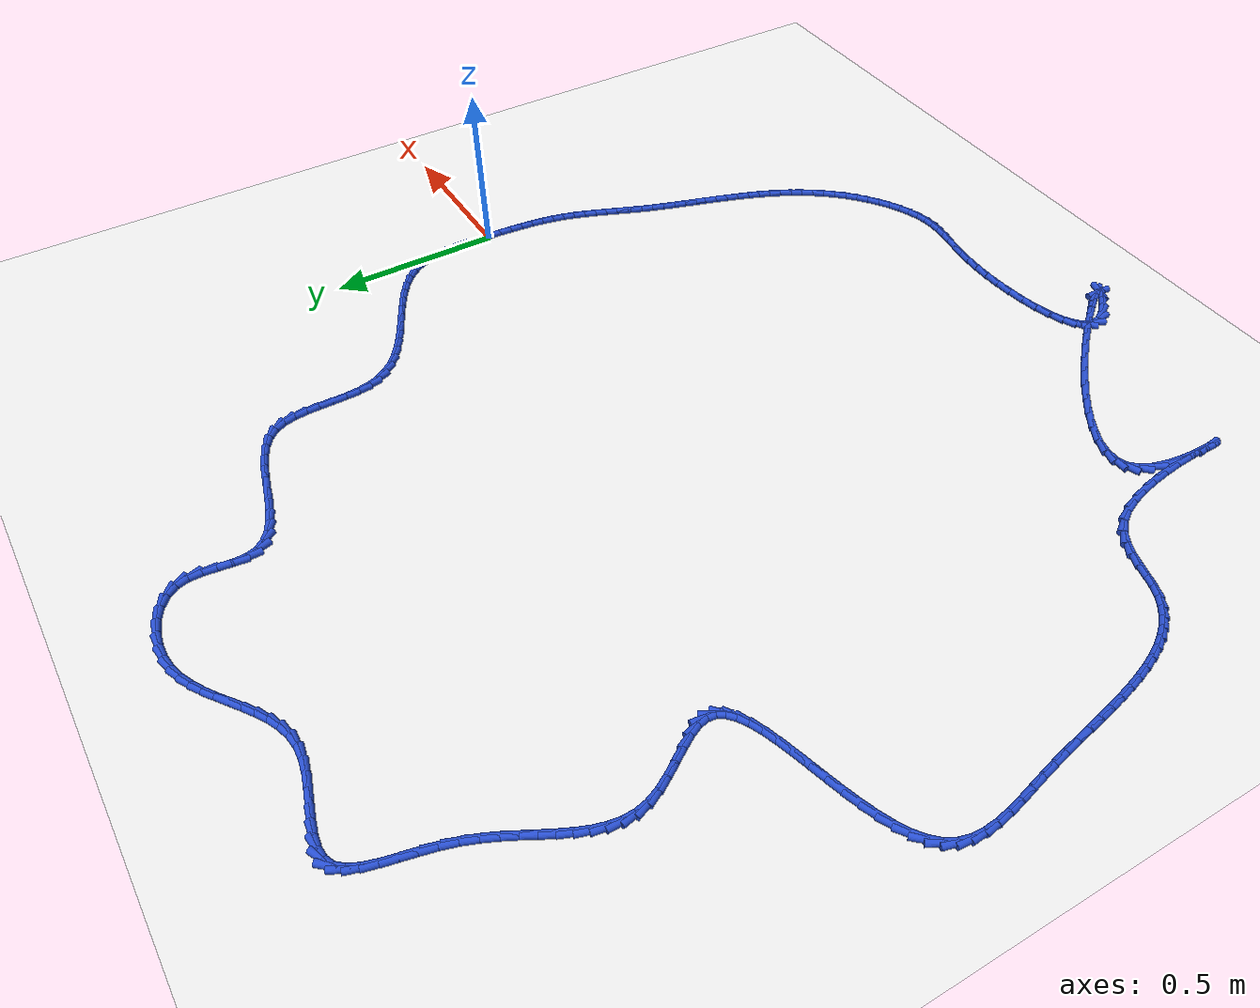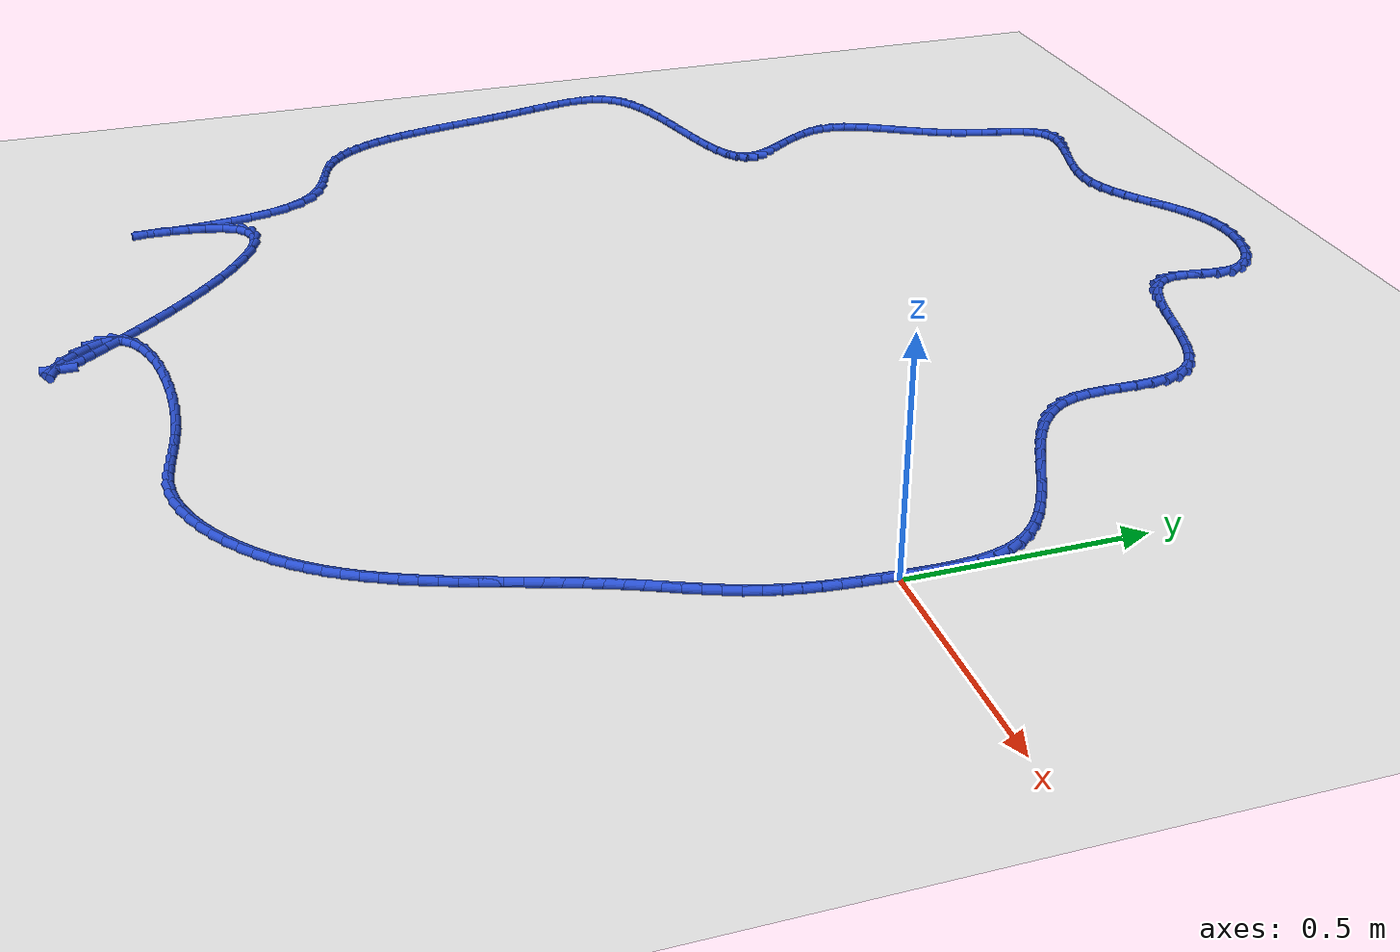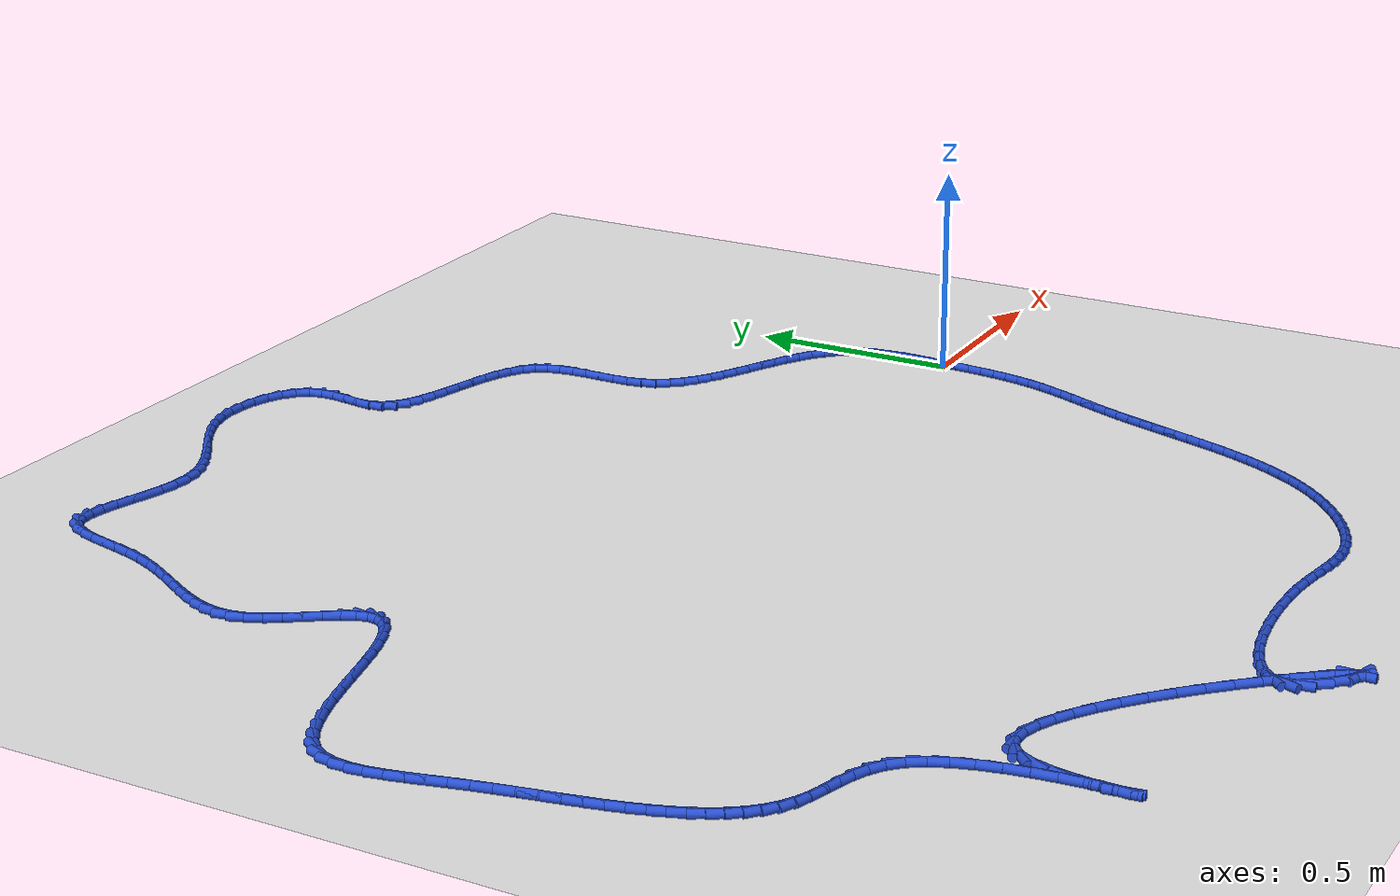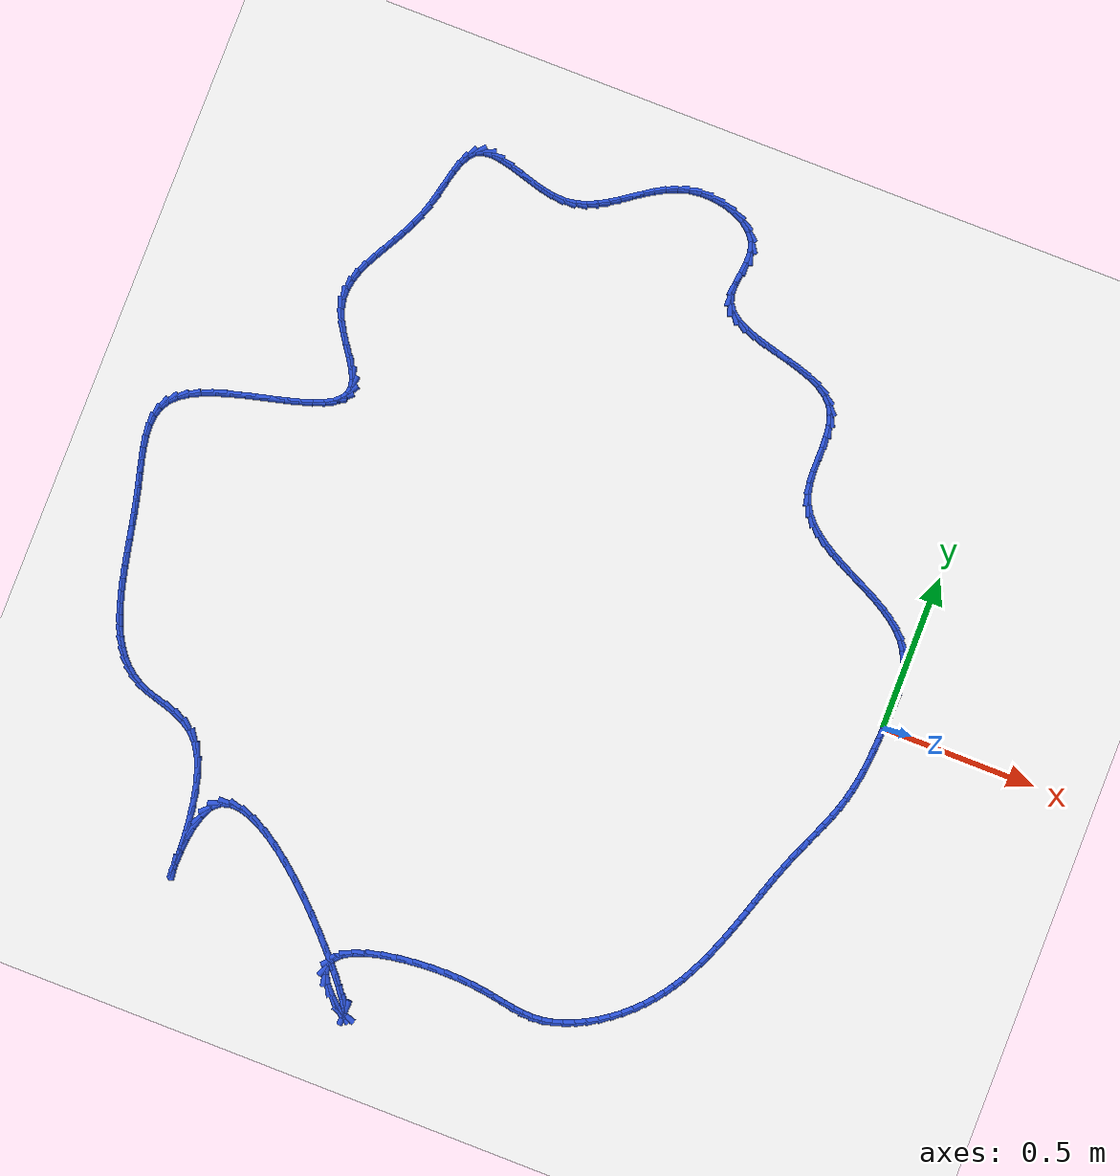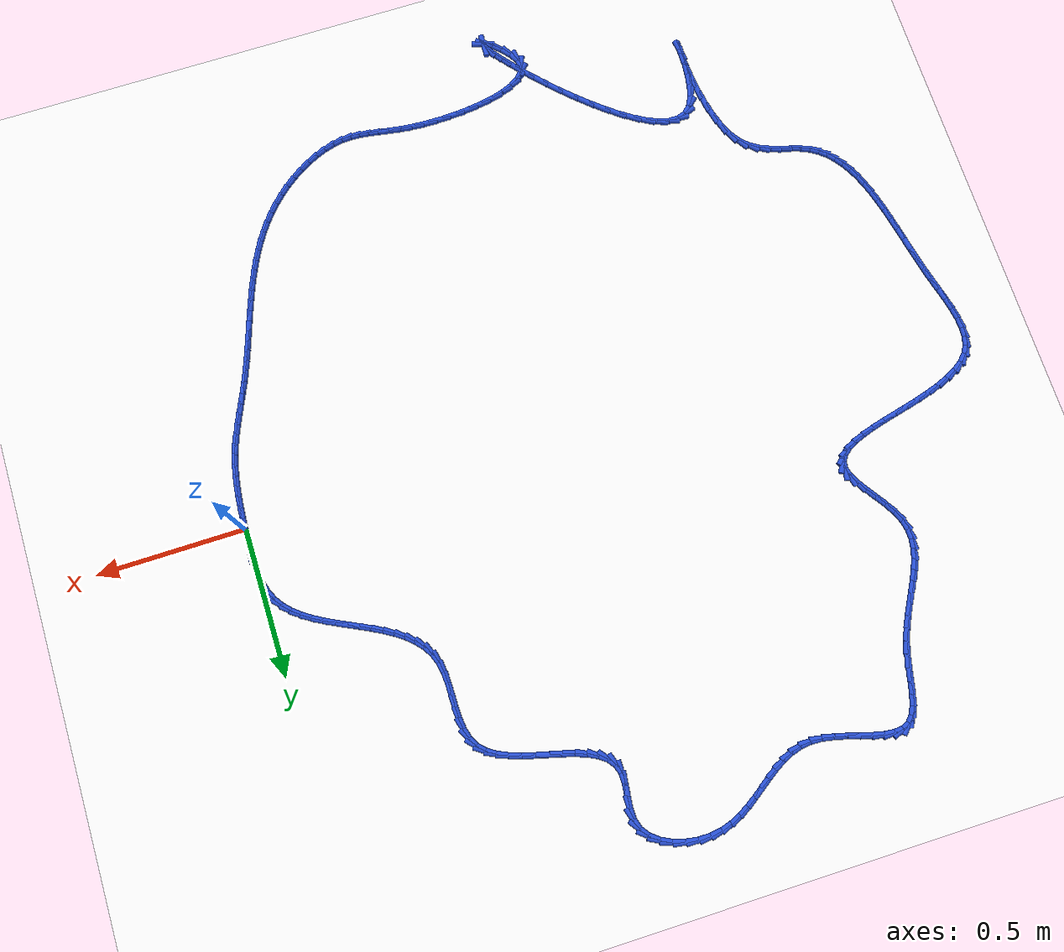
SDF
<sdf version="1.6">
 <world name="default">
  <light name="sun" type="directional">
   <pose>0 0 10 0 -0 0</pose>
   <diffuse>0.8 0.8 0.8 1</diffuse>
   <specular>0.2 0.2 0.2 1</specular>
   <attenuation>
    <range>1000</range>
    <constant>0.9</constant>
    <linear>0.01</linear>
    <quadratic>0.001</quadratic>
   </attenuation>
   <direction>-0.5 0.1 -0.9</direction>
  </light>
  <model name="ground_plane">
   <static>1</static>
   <link name="link">
    <collision name="collision">
     <geometry><plane><normal>0 0 1</normal><size>100 100</size></plane></geometry>
     <surface><friction><ode><mu>100</mu><mu2>50</mu2></ode></friction></surface>
    </collision>
    <visual name="visual">
     <cast_shadows>0</cast_shadows>
     <geometry><plane><normal>0 0 1</normal><size>100 100</size></plane></geometry>
     <material>
      <script><uri>file://media/materials/scripts/gazebo.material</uri><name>Gazebo/WhiteGlow</name></script>
     </material>
    </visual>
   </link>
  </model>
  <gravity>0 0 -9.8</gravity>
  <magnetic_field>6e-06 2.3e-05 -4.2e-05</magnetic_field>
  <atmosphere type="adiabatic"/>
  <physics name="default_physics" default="0" type="ode">
   <max_step_size>0.001</max_step_size>
   <real_time_factor>1</real_time_factor>
   <real_time_update_rate>1000</real_time_update_rate>
  </physics>
  <scene><ambient>0.4 0.4 0.4 1</ambient><background>0.7 0.7 0.7 1</background><shadows>1</shadows></scene>
  <spherical_coordinates>
   <surface_model>EARTH_WGS84</surface_model>
   <latitude_deg>0</latitude_deg>
   <longitude_deg>0</longitude_deg>
   <elevation>0</elevation>
   <heading_deg>0</heading_deg>
  </spherical_coordinates>
  <model name="line">
   <link name="link_0">
    <pose>-1.1492543028346347e-17 6.938893903907228e-18 0.01 0 1.57 1.5265133083113267</pose>
    <collision name="collision">
     <geometry><cylinder><radius>0.01</radius><length>0.08</length></cylinder></geometry>
    </collision>
    <visual name="visual">
     <material>
      <script><name>Gazebo/Blue</name><uri>file://media/materials/scripts/gazebo.material</uri></script>
     </material>
     <geometry><cylinder><radius>0.01</radius><length>0.08</length></cylinder></geometry>
    </visual>
   </link>
   <link name="link_1">
    <pose>0.0016721609055566793 0.03773608466565423 0.01 0 1.57 1.5485229028191574</pose>
    <collision name="collision">
     <geometry><cylinder><radius>0.01</radius><length>0.08</length></cylinder></geometry>
    </collision>
    <visual name="visual">
     <material>
      <script><name>Gazebo/Blue</name><uri>file://media/materials/scripts/gazebo.material</uri></script>
     </material>
     <geometry><cylinder><radius>0.01</radius><length>0.08</length></cylinder></geometry>
    </visual>
   </link>
   <link name="link_2">
    <pose>0.0025159711578495773 0.0756139928392952 0.01 0 1.57 -1.5518823976013116</pose>
    <collision name="collision">
     <geometry><cylinder><radius>0.01</radius><length>0.08</length></cylinder></geometry>
    </collision>
    <visual name="visual">
     <material>
      <script><name>Gazebo/Blue</name><uri>file://media/materials/scripts/gazebo.material</uri></script>
     </material>
     <geometry><cylinder><radius>0.01</radius><length>0.08</length></cylinder></geometry>
    </visual>
   </link>
   <link name="link_3">
    <pose>0.001807100534460578 0.1130882841108333 0.01 0 1.57 -1.4892292406859797</pose>
    <collision name="collision">
     <geometry><cylinder><radius>0.01</radius><length>0.08</length></cylinder></geometry>
    </collision>
    <visual name="visual">
     <material>
      <script><name>Gazebo/Blue</name><uri>file://media/materials/scripts/gazebo.material</uri></script>
     </material>
     <geometry><cylinder><radius>0.01</radius><length>0.08</length></cylinder></geometry>
    </visual>
   </link>
   <link name="link_4">
    <pose>-0.0011787811870284217 0.14961351807017886 0.01 0 1.57 -1.4015185372533039</pose>
    <collision name="collision">
     <geometry><cylinder><radius>0.01</radius><length>0.08</length></cylinder></geometry>
    </collision>
    <visual name="visual">
     <material>
      <script><name>Gazebo/Blue</name><uri>file://media/materials/scripts/gazebo.material</uri></script>
     </material>
     <geometry><cylinder><radius>0.01</radius><length>0.08</length></cylinder></geometry>
    </visual>
   </link>
   <link name="link_5">
    <pose>-0.007166004229035531 0.18464425430724218 0.01 0 1.57 -1.2844737737605367</pose>
    <collision name="collision">
     <geometry><cylinder><radius>0.01</radius><length>0.08</length></cylinder></geometry>
    </collision>
    <visual name="visual">
     <material>
      <script><name>Gazebo/Blue</name><uri>file://media/materials/scripts/gazebo.material</uri></script>
     </material>
     <geometry><cylinder><radius>0.01</radius><length>0.08</length></cylinder></geometry>
    </visual>
   </link>
   <link name="link_6">
    <pose>-0.016878898813978853 0.21763505241193368 0.01 0 1.57 -1.1348796790320024</pose>
    <collision name="collision">
     <geometry><cylinder><radius>0.01</radius><length>0.08</length></cylinder></geometry>
    </collision>
    <visual name="visual">
     <material>
      <script><name>Gazebo/Blue</name><uri>file://media/materials/scripts/gazebo.material</uri></script>
     </material>
     <geometry><cylinder><radius>0.01</radius><length>0.08</length></cylinder></geometry>
    </visual>
   </link>
   <link name="link_7">
    <pose>-0.03104179516427648 0.24804047197416362 0.01 0 1.57 -0.9621320333910169</pose>
    <collision name="collision">
     <geometry><cylinder><radius>0.01</radius><length>0.08</length></cylinder></geometry>
    </collision>
    <visual name="visual">
     <material>
      <script><name>Gazebo/Blue</name><uri>file://media/materials/scripts/gazebo.material</uri></script>
     </material>
     <geometry><cylinder><radius>0.01</radius><length>0.08</length></cylinder></geometry>
    </visual>
   </link>
   <link name="link_8">
    <pose>-0.05015590536359795 0.27546652729631044 0.01 0 1.57 -0.8079349664095671</pose>
    <collision name="collision">
     <geometry><cylinder><radius>0.01</radius><length>0.08</length></cylinder></geometry>
    </collision>
    <visual name="visual">
     <material>
      <script><name>Gazebo/Blue</name><uri>file://media/materials/scripts/gazebo.material</uri></script>
     </material>
     <geometry><cylinder><radius>0.01</radius><length>0.08</length></cylinder></geometry>
    </visual>
   </link>
   <link name="link_9">
    <pose>-0.07376770160157031 0.30016731919198325 0.01 0 1.57 -0.6853850154485804</pose>
    <collision name="collision">
     <geometry><cylinder><radius>0.01</radius><length>0.08</length></cylinder></geometry>
    </collision>
    <visual name="visual">
     <material>
      <script><name>Gazebo/Blue</name><uri>file://media/materials/scripts/gazebo.material</uri></script>
     </material>
     <geometry><cylinder><radius>0.01</radius><length>0.08</length></cylinder></geometry>
    </visual>
   </link>
   <link name="link_10">
    <pose>-0.10116833331812548 0.32257026398315164 0.01 0 1.57 -0.5928047303567798</pose>
    <collision name="collision">
     <geometry><cylinder><radius>0.01</radius><length>0.08</length></cylinder></geometry>
    </collision>
    <visual name="visual">
     <material>
      <script><name>Gazebo/Blue</name><uri>file://media/materials/scripts/gazebo.material</uri></script>
     </material>
     <geometry><cylinder><radius>0.01</radius><length>0.08</length></cylinder></geometry>
    </visual>
   </link>
   <link name="link_11">
    <pose>-0.13164894724163853 0.3431027798324154 0.01 0 1.57 -0.5263918821193003</pose>
    <collision name="collision">
     <geometry><cylinder><radius>0.01</radius><length>0.08</length></cylinder></geometry>
    </collision>
    <visual name="visual">
     <material>
      <script><name>Gazebo/Blue</name><uri>file://media/materials/scripts/gazebo.material</uri></script>
     </material>
     <geometry><cylinder><radius>0.01</radius><length>0.08</length></cylinder></geometry>
    </visual>
   </link>
   <link name="link_12">
    <pose>-0.1645006901004848 0.3621922849023749 0.01 0 1.57 -0.48240281276945585</pose>
    <collision name="collision">
     <geometry><cylinder><radius>0.01</radius><length>0.08</length></cylinder></geometry>
    </collision>
    <visual name="visual">
     <material>
      <script><name>Gazebo/Blue</name><uri>file://media/materials/scripts/gazebo.material</uri></script>
     </material>
     <geometry><cylinder><radius>0.01</radius><length>0.08</length></cylinder></geometry>
    </visual>
   </link>
   <link name="link_13">
    <pose>-0.19901470862303922 0.38026619735562994 0.01 0 1.57 -0.4580385133402407</pose>
    <collision name="collision">
     <geometry><cylinder><radius>0.01</radius><length>0.08</length></cylinder></geometry>
    </collision>
    <visual name="visual">
     <material>
      <script><name>Gazebo/Blue</name><uri>file://media/materials/scripts/gazebo.material</uri></script>
     </material>
     <geometry><cylinder><radius>0.01</radius><length>0.08</length></cylinder></geometry>
    </visual>
   </link>
   <link name="link_14">
    <pose>-0.23448214953767693 0.3977519353547804 0.01 0 1.57 -0.4516813231175481</pose>
    <collision name="collision">
     <geometry><cylinder><radius>0.01</radius><length>0.08</length></cylinder></geometry>
    </collision>
    <visual name="visual">
     <material>
      <script><name>Gazebo/Blue</name><uri>file://media/materials/scripts/gazebo.material</uri></script>
     </material>
     <geometry><cylinder><radius>0.01</radius><length>0.08</length></cylinder></geometry>
    </visual>
   </link>
   <link name="link_15">
    <pose>-0.27019415957277326 0.41507691706242666 0.01 0 1.57 -0.4629160748901827</pose>
    <collision name="collision">
     <geometry><cylinder><radius>0.01</radius><length>0.08</length></cylinder></geometry>
    </collision>
    <visual name="visual">
     <material>
      <script><name>Gazebo/Blue</name><uri>file://media/materials/scripts/gazebo.material</uri></script>
     </material>
     <geometry><cylinder><radius>0.01</radius><length>0.08</length></cylinder></geometry>
    </visual>
   </link>
   <link name="link_16">
    <pose>-0.3054418854567031 0.4326685606411684 0.01 0 1.57 -0.492526737449866</pose>
    <collision name="collision">
     <geometry><cylinder><radius>0.01</radius><length>0.08</length></cylinder></geometry>
    </collision>
    <visual name="visual">
     <material>
      <script><name>Gazebo/Blue</name><uri>file://media/materials/scripts/gazebo.material</uri></script>
     </material>
     <geometry><cylinder><radius>0.01</radius><length>0.08</length></cylinder></geometry>
    </visual>
   </link>
   <link name="link_17">
    <pose>-0.3395164739178418 0.45095428425360573 0.01 0 1.57 -0.5425105001039593</pose>
    <collision name="collision">
     <geometry><cylinder><radius>0.01</radius><length>0.08</length></cylinder></geometry>
    </collision>
    <visual name="visual">
     <material>
      <script><name>Gazebo/Blue</name><uri>file://media/materials/scripts/gazebo.material</uri></script>
     </material>
     <geometry><cylinder><radius>0.01</radius><length>0.08</length></cylinder></geometry>
    </visual>
   </link>
   <link name="link_18">
    <pose>-0.3717090716845643 0.47036150606233873 0.01 0 1.57 -0.6160321023677686</pose>
    <collision name="collision">
     <geometry><cylinder><radius>0.01</radius><length>0.08</length></cylinder></geometry>
    </collision>
    <visual name="visual">
     <material>
      <script><name>Gazebo/Blue</name><uri>file://media/materials/scripts/gazebo.material</uri></script>
     </material>
     <geometry><cylinder><radius>0.01</radius><length>0.08</length></cylinder></geometry>
    </visual>
   </link>
   <link name="link_19">
    <pose>-0.4013108254852458 0.4913176442299673 0.01 0 1.57 -0.7170652745694327</pose>
    <collision name="collision">
     <geometry><cylinder><radius>0.01</radius><length>0.08</length></cylinder></geometry>
    </collision>
    <visual name="visual">
     <material>
      <script><name>Gazebo/Blue</name><uri>file://media/materials/scripts/gazebo.material</uri></script>
     </material>
     <geometry><cylinder><radius>0.01</radius><length>0.08</length></cylinder></geometry>
    </visual>
   </link>
   <link name="link_20">
    <pose>-0.4276128820482615 0.5142501169190916 0.01 0 1.57 -0.8491942464901826</pose>
    <collision name="collision">
     <geometry><cylinder><radius>0.01</radius><length>0.08</length></cylinder></geometry>
    </collision>
    <visual name="visual">
     <material>
      <script><name>Gazebo/Blue</name><uri>file://media/materials/scripts/gazebo.material</uri></script>
     </material>
     <geometry><cylinder><radius>0.01</radius><length>0.08</length></cylinder></geometry>
    </visual>
   </link>
   <link name="link_21">
    <pose>-0.44990638810198647 0.5395863422923115 0.01 0 1.57 -1.0129254550661397</pose>
    <collision name="collision">
     <geometry><cylinder><radius>0.01</radius><length>0.08</length></cylinder></geometry>
    </collision>
    <visual name="visual">
     <material>
      <script><name>Gazebo/Blue</name><uri>file://media/materials/scripts/gazebo.material</uri></script>
     </material>
     <geometry><cylinder><radius>0.01</radius><length>0.08</length></cylinder></geometry>
    </visual>
   </link>
   <link name="link_22">
    <pose>-0.46748249037479583 0.567753738512227 0.01 0 1.57 -1.2018105742687184</pose>
    <collision name="collision">
     <geometry><cylinder><radius>0.01</radius><length>0.08</length></cylinder></geometry>
    </collision>
    <visual name="visual">
     <material>
      <script><name>Gazebo/Blue</name><uri>file://media/materials/scripts/gazebo.material</uri></script>
     </material>
     <geometry><cylinder><radius>0.01</radius><length>0.08</length></cylinder></geometry>
    </visual>
   </link>
   <link name="link_23">
    <pose>-0.47963433969127683 0.5991784867538567 0.01 0 1.57 -1.381108339866008</pose>
    <collision name="collision">
     <geometry><cylinder><radius>0.01</radius><length>0.08</length></cylinder></geometry>
    </collision>
    <visual name="visual">
     <material>
      <script><name>Gazebo/Blue</name><uri>file://media/materials/scripts/gazebo.material</uri></script>
     </material>
     <geometry><cylinder><radius>0.01</radius><length>0.08</length></cylinder></geometry>
    </visual>
   </link>
   <link name="link_24">
    <pose>-0.4862987250827129 0.6338894956142003 0.01 0 1.57 -1.4987221226688456</pose>
    <collision name="collision">
     <geometry><cylinder><radius>0.01</radius><length>0.08</length></cylinder></geometry>
    </collision>
    <visual name="visual">
     <material>
      <script><name>Gazebo/Blue</name><uri>file://media/materials/scripts/gazebo.material</uri></script>
     </material>
     <geometry><cylinder><radius>0.01</radius><length>0.08</length></cylinder></geometry>
    </visual>
   </link>
   <link name="link_25">
    <pose>-0.48897457284778567 0.6709514762685064 0.01 0 1.57 -1.5598760309836508</pose>
    <collision name="collision">
     <geometry><cylinder><radius>0.01</radius><length>0.08</length></cylinder></geometry>
    </collision>
    <visual name="visual">
     <material>
      <script><name>Gazebo/Blue</name><uri>file://media/materials/scripts/gazebo.material</uri></script>
     </material>
     <geometry><cylinder><radius>0.01</radius><length>0.08</length></cylinder></geometry>
    </visual>
   </link>
   <link name="link_26">
    <pose>-0.4893932104971408 0.7092856949758402 0.01 0 1.57 1.5680127551139422</pose>
    <collision name="collision">
     <geometry><cylinder><radius>0.01</radius><length>0.08</length></cylinder></geometry>
    </collision>
    <visual name="visual">
     <material>
      <script><name>Gazebo/Blue</name><uri>file://media/materials/scripts/gazebo.material</uri></script>
     </material>
     <geometry><cylinder><radius>0.01</radius><length>0.08</length></cylinder></geometry>
    </visual>
   </link>
   <link name="link_27">
    <pose>-0.48928596554142445 0.7478134179952666 0.01 0 1.57 -1.5416301258726686</pose>
    <collision name="collision">
     <geometry><cylinder><radius>0.01</radius><length>0.08</length></cylinder></geometry>
    </collision>
    <visual name="visual">
     <material>
      <script><name>Gazebo/Blue</name><uri>file://media/materials/scripts/gazebo.material</uri></script>
     </material>
     <geometry><cylinder><radius>0.01</radius><length>0.08</length></cylinder></geometry>
    </visual>
   </link>
   <link name="link_28">
    <pose>-0.4903841654912825 0.7854559115858514 0.01 0 1.57 -1.4581823588500231</pose>
    <collision name="collision">
     <geometry><cylinder><radius>0.01</radius><length>0.08</length></cylinder></geometry>
    </collision>
    <visual name="visual">
     <material>
      <script><name>Gazebo/Blue</name><uri>file://media/materials/scripts/gazebo.material</uri></script>
     </material>
     <geometry><cylinder><radius>0.01</radius><length>0.08</length></cylinder></geometry>
    </visual>
   </link>
   <link name="link_29">
    <pose>-0.49441913785736064 0.821134442006659 0.01 0 1.57 -1.310188689782235</pose>
    <collision name="collision">
     <geometry><cylinder><radius>0.01</radius><length>0.08</length></cylinder></geometry>
    </collision>
    <visual name="visual">
     <material>
      <script><name>Gazebo/Blue</name><uri>file://media/materials/scripts/gazebo.material</uri></script>
     </material>
     <geometry><cylinder><radius>0.01</radius><length>0.08</length></cylinder></geometry>
    </visual>
   </link>
   <link name="link_30">
    <pose>-0.5031222101503049 0.8537702755167552 0.01 0 1.57 -1.0837153831762578</pose>
    <collision name="collision">
     <geometry><cylinder><radius>0.01</radius><length>0.08</length></cylinder></geometry>
    </collision>
    <visual name="visual">
     <material>
      <script><name>Gazebo/Blue</name><uri>file://media/materials/scripts/gazebo.material</uri></script>
     </material>
     <geometry><cylinder><radius>0.01</radius><length>0.08</length></cylinder></geometry>
    </visual>
   </link>
   <link name="link_31">
    <pose>-0.5182247060138433 0.8822846807492724 0.01 0 1.57 -0.8064986072247172</pose>
    <collision name="collision">
     <geometry><cylinder><radius>0.01</radius><length>0.08</length></cylinder></geometry>
    </collision>
    <visual name="visual">
     <material>
      <script><name>Gazebo/Blue</name><uri>file://media/materials/scripts/gazebo.material</uri></script>
     </material>
     <geometry><cylinder><radius>0.01</radius><length>0.08</length></cylinder></geometry>
    </visual>
   </link>
   <link name="link_32">
    <pose>-0.5409022980973601 0.9059400643004443 0.01 0 1.57 -0.5830640514549351</pose>
    <collision name="collision">
     <geometry><cylinder><radius>0.01</radius><length>0.08</length></cylinder></geometry>
    </collision>
    <visual name="visual">
     <material>
      <script><name>Gazebo/Blue</name><uri>file://media/materials/scripts/gazebo.material</uri></script>
     </material>
     <geometry><cylinder><radius>0.01</radius><length>0.08</length></cylinder></geometry>
    </visual>
   </link>
   <link name="link_33">
    <pose>-0.5702340636859691 0.9252860225300399 0.01 0 1.57 -0.43083295113870296</pose>
    <collision name="collision">
     <geometry><cylinder><radius>0.01</radius><length>0.08</length></cylinder></geometry>
    </collision>
    <visual name="visual">
     <material>
      <script><name>Gazebo/Blue</name><uri>file://media/materials/scripts/gazebo.material</uri></script>
     </material>
     <geometry><cylinder><radius>0.01</radius><length>0.08</length></cylinder></geometry>
    </visual>
   </link>
   <link name="link_34">
    <pose>-0.6048046665708838 0.9411756934344973 0.01 0 1.57 -0.3331571902066949</pose>
    <collision name="collision">
     <geometry><cylinder><radius>0.01</radius><length>0.08</length></cylinder></geometry>
    </collision>
    <visual name="visual">
     <material>
      <script><name>Gazebo/Blue</name><uri>file://media/materials/scripts/gazebo.material</uri></script>
     </material>
     <geometry><cylinder><radius>0.01</radius><length>0.08</length></cylinder></geometry>
    </visual>
   </link>
   <link name="link_35">
    <pose>-0.6431987705433173 0.954462215010254 0.01 0 1.57 -0.27554943426201184</pose>
    <collision name="collision">
     <geometry><cylinder><radius>0.01</radius><length>0.08</length></cylinder></geometry>
    </collision>
    <visual name="visual">
     <material>
      <script><name>Gazebo/Blue</name><uri>file://media/materials/scripts/gazebo.material</uri></script>
     </material>
     <geometry><cylinder><radius>0.01</radius><length>0.08</length></cylinder></geometry>
    </visual>
   </link>
   <link name="link_36">
    <pose>-0.6840010393944828 0.9659987252537473 0.01 0 1.57 -0.24927202328203057</pose>
    <collision name="collision">
     <geometry><cylinder><radius>0.01</radius><length>0.08</length></cylinder></geometry>
    </collision>
    <visual name="visual">
     <material>
      <script><name>Gazebo/Blue</name><uri>file://media/materials/scripts/gazebo.material</uri></script>
     </material>
     <geometry><cylinder><radius>0.01</radius><length>0.08</length></cylinder></geometry>
    </visual>
   </link>
   <link name="link_37">
    <pose>-0.7257961369155934 0.9766383621614153 0.01 0 1.57 -0.2507201966955568</pose>
    <collision name="collision">
     <geometry><cylinder><radius>0.01</radius><length>0.08</length></cylinder></geometry>
    </collision>
    <visual name="visual">
     <material>
      <script><name>Gazebo/Blue</name><uri>file://media/materials/scripts/gazebo.material</uri></script>
     </material>
     <geometry><cylinder><radius>0.01</radius><length>0.08</length></cylinder></geometry>
    </visual>
   </link>
   <link name="link_38">
    <pose>-0.767168726897863 0.9872342637296955 0.01 0 1.57 -0.2808622549242954</pose>
    <collision name="collision">
     <geometry><cylinder><radius>0.01</radius><length>0.08</length></cylinder></geometry>
    </collision>
    <visual name="visual">
     <material>
      <script><name>Gazebo/Blue</name><uri>file://media/materials/scripts/gazebo.material</uri></script>
     </material>
     <geometry><cylinder><radius>0.01</radius><length>0.08</length></cylinder></geometry>
    </visual>
   </link>
   <link name="link_39">
    <pose>-0.8067034731325042 0.9986395679550258 0.01 0 1.57 -0.34571370823785347</pose>
    <collision name="collision">
     <geometry><cylinder><radius>0.01</radius><length>0.08</length></cylinder></geometry>
    </collision>
    <visual name="visual">
     <material>
      <script><name>Gazebo/Blue</name><uri>file://media/materials/scripts/gazebo.material</uri></script>
     </material>
     <geometry><cylinder><radius>0.01</radius><length>0.08</length></cylinder></geometry>
    </visual>
   </link>
   <link name="link_40">
    <pose>-0.8429850394107308 1.0117074128338435 0.01 0 1.57 -0.4579884233202828</pose>
    <collision name="collision">
     <geometry><cylinder><radius>0.01</radius><length>0.08</length></cylinder></geometry>
    </collision>
    <visual name="visual">
     <material>
      <script><name>Gazebo/Blue</name><uri>file://media/materials/scripts/gazebo.material</uri></script>
     </material>
     <geometry><cylinder><radius>0.01</radius><length>0.08</length></cylinder></geometry>
    </visual>
   </link>
   <link name="link_41">
    <pose>-0.8745980895237555 1.0272909363625864 0.01 0 1.57 -0.638605797465694</pose>
    <collision name="collision">
     <geometry><cylinder><radius>0.01</radius><length>0.08</length></cylinder></geometry>
    </collision>
    <visual name="visual">
     <material>
      <script><name>Gazebo/Blue</name><uri>file://media/materials/scripts/gazebo.material</uri></script>
     </material>
     <geometry><cylinder><radius>0.01</radius><length>0.08</length></cylinder></geometry>
    </visual>
   </link>
   <link name="link_42">
    <pose>-0.9001272872627917 1.0462432765376921 0.01 0 1.57 -0.9096037497589556</pose>
    <collision name="collision">
     <geometry><cylinder><radius>0.01</radius><length>0.08</length></cylinder></geometry>
    </collision>
    <visual name="visual">
     <material>
      <script><name>Gazebo/Blue</name><uri>file://media/materials/scripts/gazebo.material</uri></script>
     </material>
     <geometry><cylinder><radius>0.01</radius><length>0.08</length></cylinder></geometry>
    </visual>
   </link>
   <link name="link_43">
    <pose>-0.918157296419053 1.0694175713555982 0.01 0 1.57 -1.2586147398134726</pose>
    <collision name="collision">
     <geometry><cylinder><radius>0.01</radius><length>0.08</length></cylinder></geometry>
    </collision>
    <visual name="visual">
     <material>
      <script><name>Gazebo/Blue</name><uri>file://media/materials/scripts/gazebo.material</uri></script>
     </material>
     <geometry><cylinder><radius>0.01</radius><length>0.08</length></cylinder></geometry>
    </visual>
   </link>
   <link name="link_44">
    <pose>-0.9272741298872564 1.0976662705022981 0.01 0 1.57 -1.5647889561910269</pose>
    <collision name="collision">
     <geometry><cylinder><radius>0.01</radius><length>0.08</length></cylinder></geometry>
    </collision>
    <visual name="visual">
     <material>
      <script><name>Gazebo/Blue</name><uri>file://media/materials/scripts/gazebo.material</uri></script>
     </material>
     <geometry><cylinder><radius>0.01</radius><length>0.08</length></cylinder></geometry>
    </visual>
   </link>
   <link name="link_45">
    <pose>-0.9274751119184704 1.1311217748730886 0.01 0 1.57 1.445225749788773</pose>
    <collision name="collision">
     <geometry><cylinder><radius>0.01</radius><length>0.08</length></cylinder></geometry>
    </collision>
    <visual name="visual">
     <material>
      <script><name>Gazebo/Blue</name><uri>file://media/materials/scripts/gazebo.material</uri></script>
     </material>
     <geometry><cylinder><radius>0.01</radius><length>0.08</length></cylinder></geometry>
    </visual>
   </link>
   <link name="link_46">
    <pose>-0.9228408539802762 1.1678331987737491 0.01 0 1.57 1.4477633647388397</pose>
    <collision name="collision">
     <geometry><cylinder><radius>0.01</radius><length>0.08</length></cylinder></geometry>
    </collision>
    <visual name="visual">
     <material>
      <script><name>Gazebo/Blue</name><uri>file://media/materials/scripts/gazebo.material</uri></script>
     </material>
     <geometry><cylinder><radius>0.01</radius><length>0.08</length></cylinder></geometry>
    </visual>
   </link>
   <link name="link_47">
    <pose>-0.918186152270588 1.2054750766380515 0.01 0 1.57 -1.5669435792291668</pose>
    <collision name="collision">
     <geometry><cylinder><radius>0.01</radius><length>0.08</length></cylinder></geometry>
    </collision>
    <visual name="visual">
     <material>
      <script><name>Gazebo/Blue</name><uri>file://media/materials/scripts/gazebo.material</uri></script>
     </material>
     <geometry><cylinder><radius>0.01</radius><length>0.08</length></cylinder></geometry>
    </visual>
   </link>
   <link name="link_48">
    <pose>-0.9183258029873199 1.2417219428997683 0.01 0 1.57 -1.2855295612321902</pose>
    <collision name="collision">
     <geometry><cylinder><radius>0.01</radius><length>0.08</length></cylinder></geometry>
    </collision>
    <visual name="visual">
     <material>
      <script><name>Gazebo/Blue</name><uri>file://media/materials/scripts/gazebo.material</uri></script>
     </material>
     <geometry><cylinder><radius>0.01</radius><length>0.08</length></cylinder></geometry>
    </visual>
   </link>
   <link name="link_49">
    <pose>-0.9278819278177858 1.2743071999783715 0.01 0 1.57 -0.9452894042216033</pose>
    <collision name="collision">
     <geometry><cylinder><radius>0.01</radius><length>0.08</length></cylinder></geometry>
    </collision>
    <visual name="visual">
     <material>
      <script><name>Gazebo/Blue</name><uri>file://media/materials/scripts/gazebo.material</uri></script>
     </material>
     <geometry><cylinder><radius>0.01</radius><length>0.08</length></cylinder></geometry>
    </visual>
   </link>
   <link name="link_50">
    <pose>-0.9479199833150228 1.302050920821843 0.01 0 1.57 -0.67288594004278</pose>
    <collision name="collision">
     <geometry><cylinder><radius>0.01</radius><length>0.08</length></cylinder></geometry>
    </collision>
    <visual name="visual">
     <material>
      <script><name>Gazebo/Blue</name><uri>file://media/materials/scripts/gazebo.material</uri></script>
     </material>
     <geometry><cylinder><radius>0.01</radius><length>0.08</length></cylinder></geometry>
    </visual>
   </link>
   <link name="link_51">
    <pose>-0.9763760189339781 1.3247293084429344 0.01 0 1.57 -0.46526556914613</pose>
    <collision name="collision">
     <geometry><cylinder><radius>0.01</radius><length>0.08</length></cylinder></geometry>
    </collision>
    <visual name="visual">
     <material>
      <script><name>Gazebo/Blue</name><uri>file://media/materials/scripts/gazebo.material</uri></script>
     </material>
     <geometry><cylinder><radius>0.01</radius><length>0.08</length></cylinder></geometry>
    </visual>
   </link>
   <link name="link_52">
    <pose>-1.0110793002096736 1.3421511916244138 0.01 0 1.57 -0.29948714543218113</pose>
    <collision name="collision">
     <geometry><cylinder><radius>0.01</radius><length>0.08</length></cylinder></geometry>
    </collision>
    <visual name="visual">
     <material>
      <script><name>Gazebo/Blue</name><uri>file://media/materials/scripts/gazebo.material</uri></script>
     </material>
     <geometry><cylinder><radius>0.01</radius><length>0.08</length></cylinder></geometry>
    </visual>
   </link>
   <link name="link_53">
    <pose>-1.0498590926771316 1.3541253991490518 0.01 0 1.57 -0.15447462341094012</pose>
    <collision name="collision">
     <geometry><cylinder><radius>0.01</radius><length>0.08</length></cylinder></geometry>
    </collision>
    <visual name="visual">
     <material>
      <script><name>Gazebo/Blue</name><uri>file://media/materials/scripts/gazebo.material</uri></script>
     </material>
     <geometry><cylinder><radius>0.01</radius><length>0.08</length></cylinder></geometry>
    </visual>
   </link>
   <link name="link_54">
    <pose>-1.0905446618713748 1.3604607597996177 0.01 0 1.57 -0.012501449502034969</pose>
    <collision name="collision">
     <geometry><cylinder><radius>0.01</radius><length>0.08</length></cylinder></geometry>
    </collision>
    <visual name="visual">
     <material>
      <script><name>Gazebo/Blue</name><uri>file://media/materials/scripts/gazebo.material</uri></script>
     </material>
     <geometry><cylinder><radius>0.01</radius><length>0.08</length></cylinder></geometry>
    </visual>
   </link>
   <link name="link_55">
    <pose>-1.1309652733274256 1.3609661023588806 0.01 0 1.57 0.14050149324449962</pose>
    <collision name="collision">
     <geometry><cylinder><radius>0.01</radius><length>0.08</length></cylinder></geometry>
    </collision>
    <visual name="visual">
     <material>
      <script><name>Gazebo/Blue</name><uri>file://media/materials/scripts/gazebo.material</uri></script>
     </material>
     <geometry><cylinder><radius>0.01</radius><length>0.08</length></cylinder></geometry>
    </visual>
   </link>
   <link name="link_56">
    <pose>-1.169182039686263 1.355560975783334 0.01 0 1.57 0.2885229644580882</pose>
    <collision name="collision">
     <geometry><cylinder><radius>0.01</radius><length>0.08</length></cylinder></geometry>
    </collision>
    <visual name="visual">
     <material>
      <script><name>Gazebo/Blue</name><uri>file://media/materials/scripts/gazebo.material</uri></script>
     </material>
     <geometry><cylinder><radius>0.01</radius><length>0.08</length></cylinder></geometry>
    </visual>
   </link>
   <link name="link_57">
    <pose>-1.2049125416653537 1.3449559867070715 0.01 0 1.57 0.4127586479412599</pose>
    <collision name="collision">
     <geometry><cylinder><radius>0.01</radius><length>0.08</length></cylinder></geometry>
    </collision>
    <visual name="visual">
     <material>
      <script><name>Gazebo/Blue</name><uri>file://media/materials/scripts/gazebo.material</uri></script>
     </material>
     <geometry><cylinder><radius>0.01</radius><length>0.08</length></cylinder></geometry>
    </visual>
   </link>
   <link name="link_58">
    <pose>-1.2385950517450475 1.33020591305267 0.01 0 1.57 0.50755357179087</pose>
    <collision name="collision">
     <geometry><cylinder><radius>0.01</radius><length>0.08</length></cylinder></geometry>
    </collision>
    <visual name="visual">
     <material>
      <script><name>Gazebo/Blue</name><uri>file://media/materials/scripts/gazebo.material</uri></script>
     </material>
     <geometry><cylinder><radius>0.01</radius><length>0.08</length></cylinder></geometry>
    </visual>
   </link>
   <link name="link_59">
    <pose>-1.270670801120188 1.3123669456970783 0.01 0 1.57 0.5713561259265374</pose>
    <collision name="collision">
     <geometry><cylinder><radius>0.01</radius><length>0.08</length></cylinder></geometry>
    </collision>
    <visual name="visual">
     <material>
      <script><name>Gazebo/Blue</name><uri>file://media/materials/scripts/gazebo.material</uri></script>
     </material>
     <geometry><cylinder><radius>0.01</radius><length>0.08</length></cylinder></geometry>
    </visual>
   </link>
   <link name="link_60">
    <pose>-1.3015810209856198 1.2924952755172494 0.01 0 1.57 0.604429371227333</pose>
    <collision name="collision">
     <geometry><cylinder><radius>0.01</radius><length>0.08</length></cylinder></geometry>
    </collision>
    <visual name="visual">
     <material>
      <script><name>Gazebo/Blue</name><uri>file://media/materials/scripts/gazebo.material</uri></script>
     </material>
     <geometry><cylinder><radius>0.01</radius><length>0.08</length></cylinder></geometry>
    </visual>
   </link>
   <link name="link_61">
    <pose>-1.3317669425361864 1.2716470933901327 0.01 0 1.57 0.6070470445274952</pose>
    <collision name="collision">
     <geometry><cylinder><radius>0.01</radius><length>0.08</length></cylinder></geometry>
    </collision>
    <visual name="visual">
     <material>
      <script><name>Gazebo/Blue</name><uri>file://media/materials/scripts/gazebo.material</uri></script>
     </material>
     <geometry><cylinder><radius>0.01</radius><length>0.08</length></cylinder></geometry>
    </visual>
   </link>
   <link name="link_62">
    <pose>-1.3616697969667328 1.2508785901926798 0.01 0 1.57 0.5785463176082106</pose>
    <collision name="collision">
     <geometry><cylinder><radius>0.01</radius><length>0.08</length></cylinder></geometry>
    </collision>
    <visual name="visual">
     <material>
      <script><name>Gazebo/Blue</name><uri>file://media/materials/scripts/gazebo.material</uri></script>
     </material>
     <geometry><cylinder><radius>0.01</radius><length>0.08</length></cylinder></geometry>
    </visual>
   </link>
   <link name="link_63">
    <pose>-1.3917308154721022 1.231245956801841 0.01 0 1.57 0.5171852335132712</pose>
    <collision name="collision">
     <geometry><cylinder><radius>0.01</radius><length>0.08</length></cylinder></geometry>
    </collision>
    <visual name="visual">
     <material>
      <script><name>Gazebo/Blue</name><uri>file://media/materials/scripts/gazebo.material</uri></script>
     </material>
     <geometry><cylinder><radius>0.01</radius><length>0.08</length></cylinder></geometry>
    </visual>
   </link>
   <link name="link_64">
    <pose>-1.422391229247139 1.213805384094568 0.01 0 1.57 0.42093343493927776</pose>
    <collision name="collision">
     <geometry><cylinder><radius>0.01</radius><length>0.08</length></cylinder></geometry>
    </collision>
    <visual name="visual">
     <material>
      <script><name>Gazebo/Blue</name><uri>file://media/materials/scripts/gazebo.material</uri></script>
     </material>
     <geometry><cylinder><radius>0.01</radius><length>0.08</length></cylinder></geometry>
    </visual>
   </link>
   <link name="link_65">
    <pose>-1.4540922694866878 1.199613062947811 0.01 0 1.57 0.2896036284409017</pose>
    <collision name="collision">
     <geometry><cylinder><radius>0.01</radius><length>0.08</length></cylinder></geometry>
    </collision>
    <visual name="visual">
     <material>
      <script><name>Gazebo/Blue</name><uri>file://media/materials/scripts/gazebo.material</uri></script>
     </material>
     <geometry><cylinder><radius>0.01</radius><length>0.08</length></cylinder></geometry>
    </visual>
   </link>
   <link name="link_66">
    <pose>-1.4872751673855924 1.1897251842385215 0.01 0 1.57 0.12825151749003735</pose>
    <collision name="collision">
     <geometry><cylinder><radius>0.01</radius><length>0.08</length></cylinder></geometry>
    </collision>
    <visual name="visual">
     <material>
      <script><name>Gazebo/Blue</name><uri>file://media/materials/scripts/gazebo.material</uri></script>
     </material>
     <geometry><cylinder><radius>0.01</radius><length>0.08</length></cylinder></geometry>
    </visual>
   </link>
   <link name="link_67">
    <pose>-1.522381154138697 1.18519793884365 0.01 0 1.57 -0.044268473617673894</pose>
    <collision name="collision">
     <geometry><cylinder><radius>0.01</radius><length>0.08</length></cylinder></geometry>
    </collision>
    <visual name="visual">
     <material>
      <script><name>Gazebo/Blue</name><uri>file://media/materials/scripts/gazebo.material</uri></script>
     </material>
     <geometry><cylinder><radius>0.01</radius><length>0.08</length></cylinder></geometry>
    </visual>
   </link>
   <link name="link_68">
    <pose>-1.559739697715166 1.1868528257116457 0.01 0 1.57 -0.1725425219237369</pose>
    <collision name="collision">
     <geometry><cylinder><radius>0.01</radius><length>0.08</length></cylinder></geometry>
    </collision>
    <visual name="visual">
     <material>
      <script><name>Gazebo/Blue</name><uri>file://media/materials/scripts/gazebo.material</uri></script>
     </material>
     <geometry><cylinder><radius>0.01</radius><length>0.08</length></cylinder></geometry>
    </visual>
   </link>
   <link name="link_69">
    <pose>-1.5987985487849108 1.1936598230237523 0.01 0 1.57 -0.24743539583194793</pose>
    <collision name="collision">
     <geometry><cylinder><radius>0.01</radius><length>0.08</length></cylinder></geometry>
    </collision>
    <visual name="visual">
     <material>
      <script><name>Gazebo/Blue</name><uri>file://media/materials/scripts/gazebo.material</uri></script>
     </material>
     <geometry><cylinder><radius>0.01</radius><length>0.08</length></cylinder></geometry>
    </visual>
   </link>
   <link name="link_70">
    <pose>-1.6385873632738015 1.203710950570347 0.01 0 1.57 -0.2802427581285492</pose>
    <collision name="collision">
     <geometry><cylinder><radius>0.01</radius><length>0.08</length></cylinder></geometry>
    </collision>
    <visual name="visual">
     <material>
      <script><name>Gazebo/Blue</name><uri>file://media/materials/scripts/gazebo.material</uri></script>
     </material>
     <geometry><cylinder><radius>0.01</radius><length>0.08</length></cylinder></geometry>
    </visual>
   </link>
   <link name="link_71">
    <pose>-1.6781332811901435 1.2150929449590648 0.01 0 1.57 -0.2746325489470267</pose>
    <collision name="collision">
     <geometry><cylinder><radius>0.01</radius><length>0.08</length></cylinder></geometry>
    </collision>
    <visual name="visual">
     <material>
      <script><name>Gazebo/Blue</name><uri>file://media/materials/scripts/gazebo.material</uri></script>
     </material>
     <geometry><cylinder><radius>0.01</radius><length>0.08</length></cylinder></geometry>
    </visual>
   </link>
   <link name="link_72">
    <pose>-1.716463442542243 1.225892542797542 0.01 0 1.57 -0.2258419207506762</pose>
    <collision name="collision">
     <geometry><cylinder><radius>0.01</radius><length>0.08</length></cylinder></geometry>
    </collision>
    <visual name="visual">
     <material>
      <script><name>Gazebo/Blue</name><uri>file://media/materials/scripts/gazebo.material</uri></script>
     </material>
     <geometry><cylinder><radius>0.01</radius><length>0.08</length></cylinder></geometry>
    </visual>
   </link>
   <link name="link_73">
    <pose>-1.7526049873384053 1.2341964806934145 0.01 0 1.57 -0.11755752719931227</pose>
    <collision name="collision">
     <geometry><cylinder><radius>0.01</radius><length>0.08</length></cylinder></geometry>
    </collision>
    <visual name="visual">
     <material>
      <script><name>Gazebo/Blue</name><uri>file://media/materials/scripts/gazebo.material</uri></script>
     </material>
     <geometry><cylinder><radius>0.01</radius><length>0.08</length></cylinder></geometry>
    </visual>
   </link>
   <link name="link_74">
    <pose>-1.7855850555869375 1.2380914952543183 0.01 0 1.57 0.08394545898831744</pose>
    <collision name="collision">
     <geometry><cylinder><radius>0.01</radius><length>0.08</length></cylinder></geometry>
    </collision>
    <visual name="visual">
     <material>
      <script><name>Gazebo/Blue</name><uri>file://media/materials/scripts/gazebo.material</uri></script>
     </material>
     <geometry><cylinder><radius>0.01</radius><length>0.08</length></cylinder></geometry>
    </visual>
   </link>
   <link name="link_75">
    <pose>-1.8144307872961454 1.2356643230878888 0.01 0 1.57 0.4219861446318538</pose>
    <collision name="collision">
     <geometry><cylinder><radius>0.01</radius><length>0.08</length></cylinder></geometry>
    </collision>
    <visual name="visual">
     <material>
      <script><name>Gazebo/Blue</name><uri>file://media/materials/scripts/gazebo.material</uri></script>
     </material>
     <geometry><cylinder><radius>0.01</radius><length>0.08</length></cylinder></geometry>
    </visual>
   </link>
   <link name="link_76">
    <pose>-1.8381718254165316 1.225005620214959 0.01 0 1.57 0.8246373609502704</pose>
    <collision name="collision">
     <geometry><cylinder><radius>0.01</radius><length>0.08</length></cylinder></geometry>
    </collision>
    <visual name="visual">
     <material>
      <script><name>Gazebo/Blue</name><uri>file://media/materials/scripts/gazebo.material</uri></script>
     </material>
     <geometry><cylinder><radius>0.01</radius><length>0.08</length></cylinder></geometry>
    </visual>
   </link>
   <link name="link_77">
    <pose>-1.8564760383482382 1.2052054541698352 0.01 0 1.57 1.099918561807085</pose>
    <collision name="collision">
     <geometry><cylinder><radius>0.01</radius><length>0.08</length></cylinder></geometry>
    </collision>
    <visual name="visual">
     <material>
      <script><name>Gazebo/Blue</name><uri>file://media/materials/scripts/gazebo.material</uri></script>
     </material>
     <geometry><cylinder><radius>0.01</radius><length>0.08</length></cylinder></geometry>
    </visual>
   </link>
   <link name="link_78">
    <pose>-1.8704921253684366 1.1776727586944515 0.01 0 1.57 1.2514619019285778</pose>
    <collision name="collision">
     <geometry><cylinder><radius>0.01</radius><length>0.08</length></cylinder></geometry>
    </collision>
    <visual name="visual">
     <material>
      <script><name>Gazebo/Blue</name><uri>file://media/materials/scripts/gazebo.material</uri></script>
     </material>
     <geometry><cylinder><radius>0.01</radius><length>0.08</length></cylinder></geometry>
    </visual>
   </link>
   <link name="link_79">
    <pose>-1.8815782720392384 1.1441445067921074 0.01 0 1.57 1.3241325582827062</pose>
    <collision name="collision">
     <geometry><cylinder><radius>0.01</radius><length>0.08</length></cylinder></geometry>
    </collision>
    <visual name="visual">
     <material>
      <script><name>Gazebo/Blue</name><uri>file://media/materials/scripts/gazebo.material</uri></script>
     </material>
     <geometry><cylinder><radius>0.01</radius><length>0.08</length></cylinder></geometry>
    </visual>
   </link>
   <link name="link_80">
    <pose>-1.8910926639227563 1.1063576714661014 0.01 0 1.57 1.3440240095532634</pose>
    <collision name="collision">
     <geometry><cylinder><radius>0.01</radius><length>0.08</length></cylinder></geometry>
    </collision>
    <visual name="visual">
     <material>
      <script><name>Gazebo/Blue</name><uri>file://media/materials/scripts/gazebo.material</uri></script>
     </material>
     <geometry><cylinder><radius>0.01</radius><length>0.08</length></cylinder></geometry>
    </visual>
   </link>
   <link name="link_81">
    <pose>-1.900393486581101 1.0660492257197332 0.01 0 1.57 1.3218783087110892</pose>
    <collision name="collision">
     <geometry><cylinder><radius>0.01</radius><length>0.08</length></cylinder></geometry>
    </collision>
    <visual name="visual">
     <material>
      <script><name>Gazebo/Blue</name><uri>file://media/materials/scripts/gazebo.material</uri></script>
     </material>
     <geometry><cylinder><radius>0.01</radius><length>0.08</length></cylinder></geometry>
    </visual>
   </link>
   <link name="link_82">
    <pose>-1.910838925576385 1.024956142556302 0.01 0 1.57 1.2593751050893758</pose>
    <collision name="collision">
     <geometry><cylinder><radius>0.01</radius><length>0.08</length></cylinder></geometry>
    </collision>
    <visual name="visual">
     <material>
      <script><name>Gazebo/Blue</name><uri>file://media/materials/scripts/gazebo.material</uri></script>
     </material>
     <geometry><cylinder><radius>0.01</radius><length>0.08</length></cylinder></geometry>
    </visual>
   </link>
   <link name="link_83">
    <pose>-1.923765919452173 0.9847971375282583 0.01 0 1.57 1.1792049419602633</pose>
    <collision name="collision">
     <geometry><cylinder><radius>0.01</radius><length>0.08</length></cylinder></geometry>
    </collision>
    <visual name="visual">
     <material>
      <script><name>Gazebo/Blue</name><uri>file://media/materials/scripts/gazebo.material</uri></script>
     </material>
     <geometry><cylinder><radius>0.01</radius><length>0.08</length></cylinder></geometry>
    </visual>
   </link>
   <link name="link_84">
    <pose>-1.9395824567280096 0.9464926843374095 0.01 0 1.57 1.1173850934279785</pose>
    <collision name="collision">
     <geometry><cylinder><radius>0.01</radius><length>0.08</length></cylinder></geometry>
    </collision>
    <visual name="visual">
     <material>
      <script><name>Gazebo/Blue</name><uri>file://media/materials/scripts/gazebo.material</uri></script>
     </material>
     <geometry><cylinder><radius>0.01</radius><length>0.08</length></cylinder></geometry>
    </visual>
   </link>
   <link name="link_85">
    <pose>-1.9574265873750212 0.9098720051963848 0.01 0 1.57 1.0774778064119195</pose>
    <collision name="collision">
     <geometry><cylinder><radius>0.01</radius><length>0.08</length></cylinder></geometry>
    </collision>
    <visual name="visual">
     <material>
      <script><name>Gazebo/Blue</name><uri>file://media/materials/scripts/gazebo.material</uri></script>
     </material>
     <geometry><cylinder><radius>0.01</radius><length>0.08</length></cylinder></geometry>
    </visual>
   </link>
   <link name="link_86">
    <pose>-1.9763448197782505 0.8746856611162411 0.01 0 1.57 1.060352075614533</pose>
    <collision name="collision">
     <geometry><cylinder><radius>0.01</radius><length>0.08</length></cylinder></geometry>
    </collision>
    <visual name="visual">
     <material>
      <script><name>Gazebo/Blue</name><uri>file://media/materials/scripts/gazebo.material</uri></script>
     </material>
     <geometry><cylinder><radius>0.01</radius><length>0.08</length></cylinder></geometry>
    </visual>
   </link>
   <link name="link_87">
    <pose>-1.9953836623227366 0.8406842131080366 0.01 0 1.57 1.0674966071848522</pose>
    <collision name="collision">
     <geometry><cylinder><radius>0.01</radius><length>0.08</length></cylinder></geometry>
    </collision>
    <visual name="visual">
     <material>
      <script><name>Gazebo/Blue</name><uri>file://media/materials/scripts/gazebo.material</uri></script>
     </material>
     <geometry><cylinder><radius>0.01</radius><length>0.08</length></cylinder></geometry>
    </visual>
   </link>
   <link name="link_88">
    <pose>-2.0135896233935218 0.8076182221828299 0.01 0 1.57 1.101492141378941</pose>
    <collision name="collision">
     <geometry><cylinder><radius>0.01</radius><length>0.08</length></cylinder></geometry>
    </collision>
    <visual name="visual">
     <material>
      <script><name>Gazebo/Blue</name><uri>file://media/materials/scripts/gazebo.material</uri></script>
     </material>
     <geometry><cylinder><radius>0.01</radius><length>0.08</length></cylinder></geometry>
    </visual>
   </link>
   <link name="link_89">
    <pose>-2.0300092113756487 0.775238249351678 0.01 0 1.57 1.1661770519571342</pose>
    <collision name="collision">
     <geometry><cylinder><radius>0.01</radius><length>0.08</length></cylinder></geometry>
    </collision>
    <visual name="visual">
     <material>
      <script><name>Gazebo/Blue</name><uri>file://media/materials/scripts/gazebo.material</uri></script>
     </material>
     <geometry><cylinder><radius>0.01</radius><length>0.08</length></cylinder></geometry>
    </visual>
   </link>
   <link name="link_90">
    <pose>-2.043688934654158 0.7432948556256395 0.01 0 1.57 1.266118366930784</pose>
    <collision name="collision">
     <geometry><cylinder><radius>0.01</radius><length>0.08</length></cylinder></geometry>
    </collision>
    <visual name="visual">
     <material>
      <script><name>Gazebo/Blue</name><uri>file://media/materials/scripts/gazebo.material</uri></script>
     </material>
     <geometry><cylinder><radius>0.01</radius><length>0.08</length></cylinder></geometry>
    </visual>
   </link>
   <link name="link_91">
    <pose>-2.0536753016140907 0.7115386020157721 0.01 0 1.57 1.4045339645055368</pose>
    <collision name="collision">
     <geometry><cylinder><radius>0.01</radius><length>0.08</length></cylinder></geometry>
    </collision>
    <visual name="visual">
     <material>
      <script><name>Gazebo/Blue</name><uri>file://media/materials/scripts/gazebo.material</uri></script>
     </material>
     <geometry><cylinder><radius>0.01</radius><length>0.08</length></cylinder></geometry>
    </visual>
   </link>
   <link name="link_92">
    <pose>-2.0590148206404892 0.6797200495331343 0.01 0 1.57 -1.5626789151381304</pose>
    <collision name="collision">
     <geometry><cylinder><radius>0.01</radius><length>0.08</length></cylinder></geometry>
    </collision>
    <visual name="visual">
     <material>
      <script><name>Gazebo/Blue</name><uri>file://media/materials/scripts/gazebo.material</uri></script>
     </material>
     <geometry><cylinder><radius>0.01</radius><length>0.08</length></cylinder></geometry>
    </visual>
   </link>
   <link name="link_93">
    <pose>-2.0587540001183933 0.6475897591887835 0.01 0 1.57 -1.3652857450930833</pose>
    <collision name="collision">
     <geometry><cylinder><radius>0.01</radius><length>0.08</length></cylinder></geometry>
    </collision>
    <visual name="visual">
     <material>
      <script><name>Gazebo/Blue</name><uri>file://media/materials/scripts/gazebo.material</uri></script>
     </material>
     <geometry><cylinder><radius>0.01</radius><length>0.08</length></cylinder></geometry>
    </visual>
   </link>
   <link name="link_94">
    <pose>-2.0519393484328448 0.614898291993778 0.01 0 1.57 -1.175092285447107</pose>
    <collision name="collision">
     <geometry><cylinder><radius>0.01</radius><length>0.08</length></cylinder></geometry>
    </collision>
    <visual name="visual">
     <material>
      <script><name>Gazebo/Blue</name><uri>file://media/materials/scripts/gazebo.material</uri></script>
     </material>
     <geometry><cylinder><radius>0.01</radius><length>0.08</length></cylinder></geometry>
    </visual>
   </link>
   <link name="link_95">
    <pose>-2.037981253968023 0.5814848172712699 0.01 0 1.57 -1.0496214207186552</pose>
    <collision name="collision">
     <geometry><cylinder><radius>0.01</radius><length>0.08</length></cylinder></geometry>
    </collision>
    <visual name="visual">
     <material>
      <script><name>Gazebo/Blue</name><uri>file://media/materials/scripts/gazebo.material</uri></script>
     </material>
     <geometry><cylinder><radius>0.01</radius><length>0.08</length></cylinder></geometry>
    </visual>
   </link>
   <link name="link_96">
    <pose>-2.018616144277766 0.5477549174618606 0.01 0 1.57 -0.9860833980995647</pose>
    <collision name="collision">
     <geometry><cylinder><radius>0.01</radius><length>0.08</length></cylinder></geometry>
    </collision>
    <visual name="visual">
     <material>
      <script><name>Gazebo/Blue</name><uri>file://media/materials/scripts/gazebo.material</uri></script>
     </material>
     <geometry><cylinder><radius>0.01</radius><length>0.08</length></cylinder></geometry>
    </visual>
   </link>
   <link name="link_97">
    <pose>-1.996496070969169 0.5143371383513871 0.01 0 1.57 -0.9707467989995675</pose>
    <collision name="collision">
     <geometry><cylinder><radius>0.01</radius><length>0.08</length></cylinder></geometry>
    </collision>
    <visual name="visual">
     <material>
      <script><name>Gazebo/Blue</name><uri>file://media/materials/scripts/gazebo.material</uri></script>
     </material>
     <geometry><cylinder><radius>0.01</radius><length>0.08</length></cylinder></geometry>
    </visual>
   </link>
   <link name="link_98">
    <pose>-1.9742752883288524 0.4818605620995331 0.01 0 1.57 -1.0040763716793484</pose>
    <collision name="collision">
     <geometry><cylinder><radius>0.01</radius><length>0.08</length></cylinder></geometry>
    </collision>
    <visual name="visual">
     <material>
      <script><name>Gazebo/Blue</name><uri>file://media/materials/scripts/gazebo.material</uri></script>
     </material>
     <geometry><cylinder><radius>0.01</radius><length>0.08</length></cylinder></geometry>
    </visual>
   </link>
   <link name="link_99">
    <pose>-1.9546080506434393 0.45095427086598283 0.01 0 1.57 -1.1041997470712976</pose>
    <collision name="collision">
     <geometry><cylinder><radius>0.01</radius><length>0.08</length></cylinder></geometry>
    </collision>
    <visual name="visual">
     <material>
      <script><name>Gazebo/Blue</name><uri>file://media/materials/scripts/gazebo.material</uri></script>
     </material>
     <geometry><cylinder><radius>0.01</radius><length>0.08</length></cylinder></geometry>
    </visual>
   </link>
   <link name="link_100">
    <pose>-1.9401486121995515 0.42224734681042 0.01 0 1.57 -1.3211635936922108</pose>
    <collision name="collision">
     <geometry><cylinder><radius>0.01</radius><length>0.08</length></cylinder></geometry>
    </collision>
    <visual name="visual">
     <material>
      <script><name>Gazebo/Blue</name><uri>file://media/materials/scripts/gazebo.material</uri></script>
     </material>
     <geometry><cylinder><radius>0.01</radius><length>0.08</length></cylinder></geometry>
    </visual>
   </link>
   <link name="link_101">
    <pose>-1.933550848740114 0.3963687660289458 0.01 0 1.57 1.4339145344468494</pose>
    <collision name="collision">
     <geometry><cylinder><radius>0.01</radius><length>0.08</length></cylinder></geometry>
    </collision>
    <visual name="visual">
     <material>
      <script><name>Gazebo/Blue</name><uri>file://media/materials/scripts/gazebo.material</uri></script>
     </material>
     <geometry><cylinder><radius>0.01</radius><length>0.08</length></cylinder></geometry>
    </visual>
   </link>
   <link name="link_102">
    <pose>-1.9366700447664384 0.3737237485517861 0.01 0 1.57 1.016062376305988</pose>
    <collision name="collision">
     <geometry><cylinder><radius>0.01</radius><length>0.08</length></cylinder></geometry>
    </collision>
    <visual name="visual">
     <material>
      <script><name>Gazebo/Blue</name><uri>file://media/materials/scripts/gazebo.material</uri></script>
     </material>
     <geometry><cylinder><radius>0.01</radius><length>0.08</length></cylinder></geometry>
    </visual>
   </link>
   <link name="link_103">
    <pose>-1.9488781654335983 0.3540217169369798 0.01 0 1.57 0.7052104419745144</pose>
    <collision name="collision">
     <geometry><cylinder><radius>0.01</radius><length>0.08</length></cylinder></geometry>
    </collision>
    <visual name="visual">
     <material>
      <script><name>Gazebo/Blue</name><uri>file://media/materials/scripts/gazebo.material</uri></script>
     </material>
     <geometry><cylinder><radius>0.01</radius><length>0.08</length></cylinder></geometry>
    </visual>
   </link>
   <link name="link_104">
    <pose>-1.9690658741233529 0.3368372385304321 0.01 0 1.57 0.5087958329363389</pose>
    <collision name="collision">
     <geometry><cylinder><radius>0.01</radius><length>0.08</length></cylinder></geometry>
    </collision>
    <visual name="visual">
     <material>
      <script><name>Gazebo/Blue</name><uri>file://media/materials/scripts/gazebo.material</uri></script>
     </material>
     <geometry><cylinder><radius>0.01</radius><length>0.08</length></cylinder></geometry>
    </visual>
   </link>
   <link name="link_105">
    <pose>-1.9961238342174594 0.32174488067804874 0.01 0 1.57 0.3883126257553814</pose>
    <collision name="collision">
     <geometry><cylinder><radius>0.01</radius><length>0.08</length></cylinder></geometry>
    </collision>
    <visual name="visual">
     <material>
      <script><name>Gazebo/Blue</name><uri>file://media/materials/scripts/gazebo.material</uri></script>
     </material>
     <geometry><cylinder><radius>0.01</radius><length>0.08</length></cylinder></geometry>
    </visual>
   </link>
   <link name="link_106">
    <pose>-2.028942709097678 0.3083192107257346 0.01 0 1.57 0.3143892103237064</pose>
    <collision name="collision">
     <geometry><cylinder><radius>0.01</radius><length>0.08</length></cylinder></geometry>
    </collision>
    <visual name="visual">
     <material>
      <script><name>Gazebo/Blue</name><uri>file://media/materials/scripts/gazebo.material</uri></script>
     </material>
     <geometry><cylinder><radius>0.01</radius><length>0.08</length></cylinder></geometry>
    </visual>
   </link>
   <link name="link_107">
    <pose>-2.0664131621457673 0.2961347960193952 0.01 0 1.57 0.2704075090256907</pose>
    <collision name="collision">
     <geometry><cylinder><radius>0.01</radius><length>0.08</length></cylinder></geometry>
    </collision>
    <visual name="visual">
     <material>
      <script><name>Gazebo/Blue</name><uri>file://media/materials/scripts/gazebo.material</uri></script>
     </material>
     <geometry><cylinder><radius>0.01</radius><length>0.08</length></cylinder></geometry>
    </visual>
   </link>
   <link name="link_108">
    <pose>-2.1074258567434856 0.284766203904936 0.01 0 1.57 0.24750738505676903</pose>
    <collision name="collision">
     <geometry><cylinder><radius>0.01</radius><length>0.08</length></cylinder></geometry>
    </collision>
    <visual name="visual">
     <material>
      <script><name>Gazebo/Blue</name><uri>file://media/materials/scripts/gazebo.material</uri></script>
     </material>
     <geometry><cylinder><radius>0.01</radius><length>0.08</length></cylinder></geometry>
    </visual>
   </link>
   <link name="link_109">
    <pose>-2.1508714562725904 0.2737880017282623 0.01 0 1.57 0.24121105201070386</pose>
    <collision name="collision">
     <geometry><cylinder><radius>0.01</radius><length>0.08</length></cylinder></geometry>
    </collision>
    <visual name="visual">
     <material>
      <script><name>Gazebo/Blue</name><uri>file://media/materials/scripts/gazebo.material</uri></script>
     </material>
     <geometry><cylinder><radius>0.01</radius><length>0.08</length></cylinder></geometry>
    </visual>
   </link>
   <link name="link_110">
    <pose>-2.195640624114842 0.2627747568352795 0.01 0 1.57 0.2497406264324888</pose>
    <collision name="collision">
     <geometry><cylinder><radius>0.01</radius><length>0.08</length></cylinder></geometry>
    </collision>
    <visual name="visual">
     <material>
      <script><name>Gazebo/Blue</name><uri>file://media/materials/scripts/gazebo.material</uri></script>
     </material>
     <geometry><cylinder><radius>0.01</radius><length>0.08</length></cylinder></geometry>
    </visual>
   </link>
   <link name="link_111">
    <pose>-2.240624023651998 0.2513010365718928 0.01 0 1.57 0.27332218598845537</pose>
    <collision name="collision">
     <geometry><cylinder><radius>0.01</radius><length>0.08</length></cylinder></geometry>
    </collision>
    <visual name="visual">
     <material>
      <script><name>Gazebo/Blue</name><uri>file://media/materials/scripts/gazebo.material</uri></script>
     </material>
     <geometry><cylinder><radius>0.01</radius><length>0.08</length></cylinder></geometry>
    </visual>
   </link>
   <link name="link_112">
    <pose>-2.2847123182658162 0.23894140828400767 0.01 0 1.57 0.31409685291679196</pose>
    <collision name="collision">
     <geometry><cylinder><radius>0.01</radius><length>0.08</length></cylinder></geometry>
    </collision>
    <visual name="visual">
     <material>
      <script><name>Gazebo/Blue</name><uri>file://media/materials/scripts/gazebo.material</uri></script>
     </material>
     <geometry><cylinder><radius>0.01</radius><length>0.08</length></cylinder></geometry>
    </visual>
   </link>
   <link name="link_113">
    <pose>-2.326796171338057 0.22527043931752944 0.01 0 1.57 0.3765118272155247</pose>
    <collision name="collision">
     <geometry><cylinder><radius>0.01</radius><length>0.08</length></cylinder></geometry>
    </collision>
    <visual name="visual">
     <material>
      <script><name>Gazebo/Blue</name><uri>file://media/materials/scripts/gazebo.material</uri></script>
     </material>
     <geometry><cylinder><radius>0.01</radius><length>0.08</length></cylinder></geometry>
    </visual>
   </link>
   <link name="link_114">
    <pose>-2.3657662462504785 0.20986269701836355 0.01 0 1.57 0.4681607758998985</pose>
    <collision name="collision">
     <geometry><cylinder><radius>0.01</radius><length>0.08</length></cylinder></geometry>
    </collision>
    <visual name="visual">
     <material>
      <script><name>Gazebo/Blue</name><uri>file://media/materials/scripts/gazebo.material</uri></script>
     </material>
     <geometry><cylinder><radius>0.01</radius><length>0.08</length></cylinder></geometry>
    </visual>
   </link>
   <link name="link_115">
    <pose>-2.4005132063848387 0.19229274873241525 0.01 0 1.57 0.6007878428128963</pose>
    <collision name="collision">
     <geometry><cylinder><radius>0.01</radius><length>0.08</length></cylinder></geometry>
    </collision>
    <visual name="visual">
     <material>
      <script><name>Gazebo/Blue</name><uri>file://media/materials/scripts/gazebo.material</uri></script>
     </material>
     <geometry><cylinder><radius>0.01</radius><length>0.08</length></cylinder></geometry>
    </visual>
   </link>
   <link name="link_116">
    <pose>-2.4299277151228966 0.1721351618055899 0.01 0 1.57 0.7896877557235806</pose>
    <collision name="collision">
     <geometry><cylinder><radius>0.01</radius><length>0.08</length></cylinder></geometry>
    </collision>
    <visual name="visual">
     <material>
      <script><name>Gazebo/Blue</name><uri>file://media/materials/scripts/gazebo.material</uri></script>
     </material>
     <geometry><cylinder><radius>0.01</radius><length>0.08</length></cylinder></geometry>
    </visual>
   </link>
   <link name="link_117">
    <pose>-2.45290043584641 0.14896450358379287 0.01 0 1.57 1.039843815870917</pose>
    <collision name="collision">
     <geometry><cylinder><radius>0.01</radius><length>0.08</length></cylinder></geometry>
    </collision>
    <visual name="visual">
     <material>
      <script><name>Gazebo/Blue</name><uri>file://media/materials/scripts/gazebo.material</uri></script>
     </material>
     <geometry><cylinder><radius>0.01</radius><length>0.08</length></cylinder></geometry>
    </visual>
   </link>
   <link name="link_118">
    <pose>-2.4684885865932795 0.12241780029730995 0.01 0 1.57 1.2890645952000908</pose>
    <collision name="collision">
     <geometry><cylinder><radius>0.01</radius><length>0.08</length></cylinder></geometry>
    </collision>
    <visual name="visual">
     <material>
      <script><name>Gazebo/Blue</name><uri>file://media/materials/scripts/gazebo.material</uri></script>
     </material>
     <geometry><cylinder><radius>0.01</radius><length>0.08</length></cylinder></geometry>
    </visual>
   </link>
   <link name="link_119">
    <pose>-2.477106852226988 0.09264113547613848 0.01 0 1.57 1.4874394576556116</pose>
    <collision name="collision">
     <geometry><cylinder><radius>0.01</radius><length>0.08</length></cylinder></geometry>
    </collision>
    <visual name="visual">
     <material>
      <script><name>Gazebo/Blue</name><uri>file://media/materials/scripts/gazebo.material</uri></script>
     </material>
     <geometry><cylinder><radius>0.01</radius><length>0.08</length></cylinder></geometry>
    </visual>
   </link>
   <link name="link_120">
    <pose>-2.4798316332976933 0.06002873956207285 0.01 0 1.57 -1.5113025535465492</pose>
    <collision name="collision">
     <geometry><cylinder><radius>0.01</radius><length>0.08</length></cylinder></geometry>
    </collision>
    <visual name="visual">
     <material>
      <script><name>Gazebo/Blue</name><uri>file://media/materials/scripts/gazebo.material</uri></script>
     </material>
     <geometry><cylinder><radius>0.01</radius><length>0.08</length></cylinder></geometry>
    </visual>
   </link>
   <link name="link_121">
    <pose>-2.477743780093199 0.024976511672255917 0.01 0 1.57 -1.4151848821336794</pose>
    <collision name="collision">
     <geometry><cylinder><radius>0.01</radius><length>0.08</length></cylinder></geometry>
    </collision>
    <visual name="visual">
     <material>
      <script><name>Gazebo/Blue</name><uri>file://media/materials/scripts/gazebo.material</uri></script>
     </material>
     <geometry><cylinder><radius>0.01</radius><length>0.08</length></cylinder></geometry>
    </visual>
   </link>
   <link name="link_122">
    <pose>-2.471924142901306 -0.01211964907616823 0.01 0 1.57 -1.3555549321891036</pose>
    <collision name="collision">
     <geometry><cylinder><radius>0.01</radius><length>0.08</length></cylinder></geometry>
    </collision>
    <visual name="visual">
     <material>
      <script><name>Gazebo/Blue</name><uri>file://media/materials/scripts/gazebo.material</uri></script>
     </material>
     <geometry><cylinder><radius>0.01</radius><length>0.08</length></cylinder></geometry>
    </visual>
   </link>
   <link name="link_123">
    <pose>-2.4634535720098194 -0.050863843566055854 0.01 0 1.57 -1.3248396481028193</pose>
    <collision name="collision">
     <geometry><cylinder><radius>0.01</radius><length>0.08</length></cylinder></geometry>
    </collision>
    <visual name="visual">
     <material>
      <script><name>Gazebo/Blue</name><uri>file://media/materials/scripts/gazebo.material</uri></script>
     </material>
     <geometry><cylinder><radius>0.01</radius><length>0.08</length></cylinder></geometry>
    </visual>
   </link>
   <link name="link_124">
    <pose>-2.4534129177065394 -0.0908601726802632 0.01 0 1.57 -1.3185337633686185</pose>
    <collision name="collision">
     <geometry><cylinder><radius>0.01</radius><length>0.08</length></cylinder></geometry>
    </collision>
    <visual name="visual">
     <material>
      <script><name>Gazebo/Blue</name><uri>file://media/materials/scripts/gazebo.material</uri></script>
     </material>
     <geometry><cylinder><radius>0.01</radius><length>0.08</length></cylinder></geometry>
    </visual>
   </link>
   <link name="link_125">
    <pose>-2.442883030279271 -0.1317127373016466 0.01 0 1.57 -1.3333563167471236</pose>
    <collision name="collision">
     <geometry><cylinder><radius>0.01</radius><length>0.08</length></cylinder></geometry>
    </collision>
    <visual name="visual">
     <material>
      <script><name>Gazebo/Blue</name><uri>file://media/materials/scripts/gazebo.material</uri></script>
     </material>
     <geometry><cylinder><radius>0.01</radius><length>0.08</length></cylinder></geometry>
    </visual>
   </link>
   <link name="link_126">
    <pose>-2.432883216422593 -0.1730334118090449 0.01 0 1.57 -1.3525245720255827</pose>
    <collision name="collision">
     <geometry><cylinder><radius>0.01</radius><length>0.08</length></cylinder></geometry>
    </collision>
    <visual name="visual">
     <material>
      <script><name>Gazebo/Blue</name><uri>file://media/materials/scripts/gazebo.material</uri></script>
     </material>
     <geometry><cylinder><radius>0.01</radius><length>0.08</length></cylinder></geometry>
    </visual>
   </link>
   <link name="link_127">
    <pose>-2.423679212520789 -0.21452925312545781 0.01 0 1.57 -1.3650852002588931</pose>
    <collision name="collision">
     <geometry><cylinder><radius>0.01</radius><length>0.08</length></cylinder></geometry>
    </collision>
    <visual name="visual">
     <material>
      <script><name>Gazebo/Blue</name><uri>file://media/materials/scripts/gazebo.material</uri></script>
     </material>
     <geometry><cylinder><radius>0.01</radius><length>0.08</length></cylinder></geometry>
    </visual>
   </link>
   <link name="link_128">
    <pose>-2.415031842316191 -0.2559710930721039 0.01 0 1.57 -1.3708967290803313</pose>
    <collision name="collision">
     <geometry><cylinder><radius>0.01</radius><length>0.08</length></cylinder></geometry>
    </collision>
    <visual name="visual">
     <material>
      <script><name>Gazebo/Blue</name><uri>file://media/materials/scripts/gazebo.material</uri></script>
     </material>
     <geometry><cylinder><radius>0.01</radius><length>0.08</length></cylinder></geometry>
    </visual>
   </link>
   <link name="link_129">
    <pose>-2.4066926309634704 -0.29713093796343554 0.01 0 1.57 -1.3698656576040704</pose>
    <collision name="collision">
     <geometry><cylinder><radius>0.01</radius><length>0.08</length></cylinder></geometry>
    </collision>
    <visual name="visual">
     <material>
      <script><name>Gazebo/Blue</name><uri>file://media/materials/scripts/gazebo.material</uri></script>
     </material>
     <geometry><cylinder><radius>0.01</radius><length>0.08</length></cylinder></geometry>
    </visual>
   </link>
   <link name="link_130">
    <pose>-2.3984131036172975 -0.33778079411390505 0.01 0 1.57 -1.3617215200044916</pose>
    <collision name="collision">
     <geometry><cylinder><radius>0.01</radius><length>0.08</length></cylinder></geometry>
    </collision>
    <visual name="visual">
     <material>
      <script><name>Gazebo/Blue</name><uri>file://media/materials/scripts/gazebo.material</uri></script>
     </material>
     <geometry><cylinder><radius>0.01</radius><length>0.08</length></cylinder></geometry>
    </visual>
   </link>
   <link name="link_131">
    <pose>-2.3899447854323443 -0.37769266783796485 0.01 0 1.57 -1.345995741973674</pose>
    <collision name="collision">
     <geometry><cylinder><radius>0.01</radius><length>0.08</length></cylinder></geometry>
    </collision>
    <visual name="visual">
     <material>
      <script><name>Gazebo/Blue</name><uri>file://media/materials/scripts/gazebo.material</uri></script>
     </material>
     <geometry><cylinder><radius>0.01</radius><length>0.08</length></cylinder></geometry>
    </visual>
   </link>
   <link name="link_132">
    <pose>-2.3810392015632824 -0.41663856545006717 0.01 0 1.57 -1.321998420329714</pose>
    <collision name="collision">
     <geometry><cylinder><radius>0.01</radius><length>0.08</length></cylinder></geometry>
    </collision>
    <visual name="visual">
     <material>
      <script><name>Gazebo/Blue</name><uri>file://media/materials/scripts/gazebo.material</uri></script>
     </material>
     <geometry><cylinder><radius>0.01</radius><length>0.08</length></cylinder></geometry>
    </visual>
   </link>
   <link name="link_133">
    <pose>-2.3714478771647816 -0.4543904932646642 0.01 0 1.57 -1.288796631365471</pose>
    <collision name="collision">
     <geometry><cylinder><radius>0.01</radius><length>0.08</length></cylinder></geometry>
    </collision>
    <visual name="visual">
     <material>
      <script><name>Gazebo/Blue</name><uri>file://media/materials/scripts/gazebo.material</uri></script>
     </material>
     <geometry><cylinder><radius>0.01</radius><length>0.08</length></cylinder></geometry>
    </visual>
   </link>
   <link name="link_134">
    <pose>-2.360922337391514 -0.49072045759620864 0.01 0 1.57 -1.2452039810648723</pose>
    <collision name="collision">
     <geometry><cylinder><radius>0.01</radius><length>0.08</length></cylinder></geometry>
    </collision>
    <visual name="visual">
     <material>
      <script><name>Gazebo/Blue</name><uri>file://media/materials/scripts/gazebo.material</uri></script>
     </material>
     <geometry><cylinder><radius>0.01</radius><length>0.08</length></cylinder></geometry>
    </visual>
   </link>
   <link name="link_135">
    <pose>-2.3492141073981507 -0.5254004647591526 0.01 0 1.57 -1.1898019412637397</pose>
    <collision name="collision">
     <geometry><cylinder><radius>0.01</radius><length>0.08</length></cylinder></geometry>
    </collision>
    <visual name="visual">
     <material>
      <script><name>Gazebo/Blue</name><uri>file://media/materials/scripts/gazebo.material</uri></script>
     </material>
     <geometry><cylinder><radius>0.01</radius><length>0.08</length></cylinder></geometry>
    </visual>
   </link>
   <link name="link_136">
    <pose>-2.336074712339363 -0.5582025210679484 0.01 0 1.57 -1.121030838147792</pose>
    <collision name="collision">
     <geometry><cylinder><radius>0.01</radius><length>0.08</length></cylinder></geometry>
    </collision>
    <visual name="visual">
     <material>
      <script><name>Gazebo/Blue</name><uri>file://media/materials/scripts/gazebo.material</uri></script>
     </material>
     <geometry><cylinder><radius>0.01</radius><length>0.08</length></cylinder></geometry>
    </visual>
   </link>
   <link name="link_137">
    <pose>-2.3212556773698214 -0.5888986328370485 0.01 0 1.57 -1.0374100649282034</pose>
    <collision name="collision">
     <geometry><cylinder><radius>0.01</radius><length>0.08</length></cylinder></geometry>
    </collision>
    <visual name="visual">
     <material>
      <script><name>Gazebo/Blue</name><uri>file://media/materials/scripts/gazebo.material</uri></script>
     </material>
     <geometry><cylinder><radius>0.01</radius><length>0.08</length></cylinder></geometry>
    </visual>
   </link>
   <link name="link_138">
    <pose>-2.304508527644198 -0.6172608063809051 0.01 0 1.57 -0.937957715069525</pose>
    <collision name="collision">
     <geometry><cylinder><radius>0.01</radius><length>0.08</length></cylinder></geometry>
    </collision>
    <visual name="visual">
     <material>
      <script><name>Gazebo/Blue</name><uri>file://media/materials/scripts/gazebo.material</uri></script>
     </material>
     <geometry><cylinder><radius>0.01</radius><length>0.08</length></cylinder></geometry>
    </visual>
   </link>
   <link name="link_139">
    <pose>-2.2855847883171636 -0.6430610480139707 0.01 0 1.57 -0.8228365958755302</pose>
    <collision name="collision">
     <geometry><cylinder><radius>0.01</radius><length>0.08</length></cylinder></geometry>
    </collision>
    <visual name="visual">
     <material>
      <script><name>Gazebo/Blue</name><uri>file://media/materials/scripts/gazebo.material</uri></script>
     </material>
     <geometry><cylinder><radius>0.01</radius><length>0.08</length></cylinder></geometry>
    </visual>
   </link>
   <link name="link_140">
    <pose>-2.2642359845433893 -0.6660713640506974 0.01 0 1.57 -0.6940937152403519</pose>
    <collision name="collision">
     <geometry><cylinder><radius>0.01</radius><length>0.08</length></cylinder></geometry>
    </collision>
    <visual name="visual">
     <material>
      <script><name>Gazebo/Blue</name><uri>file://media/materials/scripts/gazebo.material</uri></script>
     </material>
     <geometry><cylinder><radius>0.01</radius><length>0.08</length></cylinder></geometry>
    </visual>
   </link>
   <link name="link_141">
    <pose>-2.2402136414775464 -0.686063760805538 0.01 0 1.57 -0.5560936486939497</pose>
    <collision name="collision">
     <geometry><cylinder><radius>0.01</radius><length>0.08</length></cylinder></geometry>
    </collision>
    <visual name="visual">
     <material>
      <script><name>Gazebo/Blue</name><uri>file://media/materials/scripts/gazebo.material</uri></script>
     </material>
     <geometry><cylinder><radius>0.01</radius><length>0.08</length></cylinder></geometry>
    </visual>
   </link>
   <link name="link_142">
    <pose>-2.213269284274306 -0.7028102445929443 0.01 0 1.57 -0.4161811387619457</pose>
    <collision name="collision">
     <geometry><cylinder><radius>0.01</radius><length>0.08</length></cylinder></geometry>
    </collision>
    <visual name="visual">
     <material>
      <script><name>Gazebo/Blue</name><uri>file://media/materials/scripts/gazebo.material</uri></script>
     </material>
     <geometry><cylinder><radius>0.01</radius><length>0.08</length></cylinder></geometry>
    </visual>
   </link>
   <link name="link_143">
    <pose>-2.183174413365323 -0.7161121738285997 0.01 0 1.57 -0.3130130268917556</pose>
    <collision name="collision">
     <geometry><cylinder><radius>0.01</radius><length>0.08</length></cylinder></geometry>
    </collision>
    <visual name="visual">
     <material>
      <script><name>Gazebo/Blue</name><uri>file://media/materials/scripts/gazebo.material</uri></script>
     </material>
     <geometry><cylinder><radius>0.01</radius><length>0.08</length></cylinder></geometry>
    </visual>
   </link>
   <link name="link_144">
    <pose>-2.1503559326440493 -0.7267339708583302 0.01 0 1.57 -0.2797789869635331</pose>
    <collision name="collision">
     <geometry><cylinder><radius>0.01</radius><length>0.08</length></cylinder></geometry>
    </collision>
    <visual name="visual">
     <material>
      <script><name>Gazebo/Blue</name><uri>file://media/materials/scripts/gazebo.material</uri></script>
     </material>
     <geometry><cylinder><radius>0.01</radius><length>0.08</length></cylinder></geometry>
    </visual>
   </link>
   <link name="link_145">
    <pose>-2.11602802087698 -0.7365968966434566 0.01 0 1.57 -0.31047247829978486</pose>
    <collision name="collision">
     <geometry><cylinder><radius>0.01</radius><length>0.08</length></cylinder></geometry>
    </collision>
    <visual name="visual">
     <material>
      <script><name>Gazebo/Blue</name><uri>file://media/materials/scripts/gazebo.material</uri></script>
     </material>
     <geometry><cylinder><radius>0.01</radius><length>0.08</length></cylinder></geometry>
    </visual>
   </link>
   <link name="link_146">
    <pose>-2.0814514845681753 -0.7476907279448258 0.01 0 1.57 -0.40312324345795586</pose>
    <collision name="collision">
     <geometry><cylinder><radius>0.01</radius><length>0.08</length></cylinder></geometry>
    </collision>
    <visual name="visual">
     <material>
      <script><name>Gazebo/Blue</name><uri>file://media/materials/scripts/gazebo.material</uri></script>
     </material>
     <geometry><cylinder><radius>0.01</radius><length>0.08</length></cylinder></geometry>
    </visual>
   </link>
   <link name="link_147">
    <pose>-2.0478871302217 -0.7620052415232837 0.01 0 1.57 -0.5578605766019754</pose>
    <collision name="collision">
     <geometry><cylinder><radius>0.01</radius><length>0.08</length></cylinder></geometry>
    </collision>
    <visual name="visual">
     <material>
      <script><name>Gazebo/Blue</name><uri>file://media/materials/scripts/gazebo.material</uri></script>
     </material>
     <geometry><cylinder><radius>0.01</radius><length>0.08</length></cylinder></geometry>
    </visual>
   </link>
   <link name="link_148">
    <pose>-2.016595764341615 -0.7815302141396764 0.01 0 1.57 -0.7664520123413866</pose>
    <collision name="collision">
     <geometry><cylinder><radius>0.01</radius><length>0.08</length></cylinder></geometry>
    </collision>
    <visual name="visual">
     <material>
      <script><name>Gazebo/Blue</name><uri>file://media/materials/scripts/gazebo.material</uri></script>
     </material>
     <geometry><cylinder><radius>0.01</radius><length>0.08</length></cylinder></geometry>
    </visual>
   </link>
   <link name="link_149">
    <pose>-1.9888381934319856 -0.8082554225548505 0.01 0 1.57 -0.9933609812040997</pose>
    <collision name="collision">
     <geometry><cylinder><radius>0.01</radius><length>0.08</length></cylinder></geometry>
    </collision>
    <visual name="visual">
     <material>
      <script><name>Gazebo/Blue</name><uri>file://media/materials/scripts/gazebo.material</uri></script>
     </material>
     <geometry><cylinder><radius>0.01</radius><length>0.08</length></cylinder></geometry>
    </visual>
   </link>
   <link name="link_150">
    <pose>-1.9657119761763013 -0.843751808380879 0.01 0 1.57 -1.1637436459038697</pose>
    <collision name="collision">
     <geometry><cylinder><radius>0.01</radius><length>0.08</length></cylinder></geometry>
    </collision>
    <visual name="visual">
     <material>
      <script><name>Gazebo/Blue</name><uri>file://media/materials/scripts/gazebo.material</uri></script>
     </material>
     <geometry><cylinder><radius>0.01</radius><length>0.08</length></cylinder></geometry>
    </visual>
   </link>
   <link name="link_151">
    <pose>-1.9471916994690344 -0.8867091718175285 0.01 0 1.57 -1.2785103189010771</pose>
    <collision name="collision">
     <geometry><cylinder><radius>0.01</radius><length>0.08</length></cylinder></geometry>
    </collision>
    <visual name="visual">
     <material>
      <script><name>Gazebo/Blue</name><uri>file://media/materials/scripts/gazebo.material</uri></script>
     </material>
     <geometry><cylinder><radius>0.01</radius><length>0.08</length></cylinder></geometry>
    </visual>
   </link>
   <link name="link_152">
    <pose>-1.9327795547486228 -0.9346053163566493 0.01 0 1.57 -1.3592647021777633</pose>
    <collision name="collision">
     <geometry><cylinder><radius>0.01</radius><length>0.08</length></cylinder></geometry>
    </collision>
    <visual name="visual">
     <material>
      <script><name>Gazebo/Blue</name><uri>file://media/materials/scripts/gazebo.material</uri></script>
     </material>
     <geometry><cylinder><radius>0.01</radius><length>0.08</length></cylinder></geometry>
    </visual>
   </link>
   <link name="link_153">
    <pose>-1.9219760930564305 -0.9849138368216397 0.01 0 1.57 -1.418692011305713</pose>
    <collision name="collision">
     <geometry><cylinder><radius>0.01</radius><length>0.08</length></cylinder></geometry>
    </collision>
    <visual name="visual">
     <material>
      <script><name>Gazebo/Blue</name><uri>file://media/materials/scripts/gazebo.material</uri></script>
     </material>
     <geometry><cylinder><radius>0.01</radius><length>0.08</length></cylinder></geometry>
    </visual>
   </link>
   <link name="link_154">
    <pose>-1.914281865433821 -1.0351083280358986 0.01 0 1.57 -1.4642817614699033</pose>
    <collision name="collision">
     <geometry><cylinder><radius>0.01</radius><length>0.08</length></cylinder></geometry>
    </collision>
    <visual name="visual">
     <material>
      <script><name>Gazebo/Blue</name><uri>file://media/materials/scripts/gazebo.material</uri></script>
     </material>
     <geometry><cylinder><radius>0.01</radius><length>0.08</length></cylinder></geometry>
    </visual>
   </link>
   <link name="link_155">
    <pose>-1.9091974229221589 -1.0826623848228245 0.01 0 1.57 -1.5007459610336376</pose>
    <collision name="collision">
     <geometry><cylinder><radius>0.01</radius><length>0.08</length></cylinder></geometry>
    </collision>
    <visual name="visual">
     <material>
      <script><name>Gazebo/Blue</name><uri>file://media/materials/scripts/gazebo.material</uri></script>
     </material>
     <geometry><cylinder><radius>0.01</radius><length>0.08</length></cylinder></geometry>
    </visual>
   </link>
   <link name="link_156">
    <pose>-1.9062233165628069 -1.1250496020058158 0.01 0 1.57 -1.5315238493070107</pose>
    <collision name="collision">
     <geometry><cylinder><radius>0.01</radius><length>0.08</length></cylinder></geometry>
    </collision>
    <visual name="visual">
     <material>
      <script><name>Gazebo/Blue</name><uri>file://media/materials/scripts/gazebo.material</uri></script>
     </material>
     <geometry><cylinder><radius>0.01</radius><length>0.08</length></cylinder></geometry>
    </visual>
   </link>
   <link name="link_157">
    <pose>-1.9048600973971297 -1.159743574408271 0.01 0 1.57 -1.5605091350062055</pose>
    <collision name="collision">
     <geometry><cylinder><radius>0.01</radius><length>0.08</length></cylinder></geometry>
    </collision>
    <visual name="visual">
     <material>
      <script><name>Gazebo/Blue</name><uri>file://media/materials/scripts/gazebo.material</uri></script>
     </material>
     <geometry><cylinder><radius>0.01</radius><length>0.08</length></cylinder></geometry>
    </visual>
   </link>
   <link name="link_158">
    <pose>-1.904608316466491 -1.1842178968535888 0.01 0 1.57 1.5400931426541125</pose>
    <collision name="collision">
     <geometry><cylinder><radius>0.01</radius><length>0.08</length></cylinder></geometry>
    </collision>
    <visual name="visual">
     <material>
      <script><name>Gazebo/Blue</name><uri>file://media/materials/scripts/gazebo.material</uri></script>
     </material>
     <geometry><cylinder><radius>0.01</radius><length>0.08</length></cylinder></geometry>
    </visual>
   </link>
   <link name="link_159">
    <pose>-1.904968524812255 -1.1959461641651676 0.01 0 1.57 -1.4381922341594515</pose>
    <collision name="collision">
     <geometry><cylinder><radius>0.01</radius><length>0.08</length></cylinder></geometry>
    </collision>
    <visual name="visual">
     <material>
      <script><name>Gazebo/Blue</name><uri>file://media/materials/scripts/gazebo.material</uri></script>
     </material>
     <geometry><cylinder><radius>0.01</radius><length>0.08</length></cylinder></geometry>
    </visual>
   </link>
   <link name="link_160">
    <pose>-1.9054412734757853 -1.1924019711664067 0.01 0 1.57 -1.5706328962005065</pose>
    <collision name="collision">
     <geometry><cylinder><radius>0.01</radius><length>0.08</length></cylinder></geometry>
    </collision>
    <visual name="visual">
     <material>
      <script><name>Gazebo/Blue</name><uri>file://media/materials/scripts/gazebo.material</uri></script>
     </material>
     <geometry><cylinder><radius>0.01</radius><length>0.08</length></cylinder></geometry>
    </visual>
   </link>
   <link name="link_161">
    <pose>-1.90544455852294 -1.1723014071456057 0.01 0 1.57 1.5286655876502104</pose>
    <collision name="collision">
     <geometry><cylinder><radius>0.01</radius><length>0.08</length></cylinder></geometry>
    </collision>
    <visual name="visual">
     <material>
      <script><name>Gazebo/Blue</name><uri>file://media/materials/scripts/gazebo.material</uri></script>
     </material>
     <geometry><cylinder><radius>0.01</radius><length>0.08</length></cylinder></geometry>
    </visual>
   </link>
   <link name="link_162">
    <pose>-1.9040591158367315 -1.1394364990660397 0.01 0 1.57 1.4778376806809477</pose>
    <collision name="collision">
     <geometry><cylinder><radius>0.01</radius><length>0.08</length></cylinder></geometry>
    </collision>
    <visual name="visual">
     <material>
      <script><name>Gazebo/Blue</name><uri>file://media/materials/scripts/gazebo.material</uri></script>
     </material>
     <geometry><cylinder><radius>0.01</radius><length>0.08</length></cylinder></geometry>
    </visual>
   </link>
   <link name="link_163">
    <pose>-1.9002795688216205 -1.0988953105901944 0.01 0 1.57 1.405855341882933</pose>
    <collision name="collision">
     <geometry><cylinder><radius>0.01</radius><length>0.08</length></cylinder></geometry>
    </collision>
    <visual name="visual">
     <material>
      <script><name>Gazebo/Blue</name><uri>file://media/materials/scripts/gazebo.material</uri></script>
     </material>
     <geometry><cylinder><radius>0.01</radius><length>0.08</length></cylinder></geometry>
    </visual>
   </link>
   <link name="link_164">
    <pose>-1.89310054085275 -1.0557659058218027 0.01 0 1.57 1.29305560544293</pose>
    <collision name="collision">
     <geometry><cylinder><radius>0.01</radius><length>0.08</length></cylinder></geometry>
    </collision>
    <visual name="visual">
     <material>
      <script><name>Gazebo/Blue</name><uri>file://media/materials/scripts/gazebo.material</uri></script>
     </material>
     <geometry><cylinder><radius>0.01</radius><length>0.08</length></cylinder></geometry>
    </visual>
   </link>
   <link name="link_165">
    <pose>-1.8815166553052634 -1.0151363488645972 0.01 0 1.57 1.0957550850307063</pose>
    <collision name="collision">
     <geometry><cylinder><radius>0.01</radius><length>0.08</length></cylinder></geometry>
    </collision>
    <visual name="visual">
     <material>
      <script><name>Gazebo/Blue</name><uri>file://media/materials/scripts/gazebo.material</uri></script>
     </material>
     <geometry><cylinder><radius>0.01</radius><length>0.08</length></cylinder></geometry>
    </visual>
   </link>
   <link name="link_166">
    <pose>-1.864522535554304 -0.9820947038223105 0.01 0 1.57 0.743063597456006</pose>
    <collision name="collision">
     <geometry><cylinder><radius>0.01</radius><length>0.08</length></cylinder></geometry>
    </collision>
    <visual name="visual">
     <material>
      <script><name>Gazebo/Blue</name><uri>file://media/materials/scripts/gazebo.material</uri></script>
     </material>
     <geometry><cylinder><radius>0.01</radius><length>0.08</length></cylinder></geometry>
    </visual>
   </link>
   <link name="link_167">
    <pose>-1.8413744357397341 -0.9608280091492051 0.01 0 1.57 0.31774739328956525</pose>
    <collision name="collision">
     <geometry><cylinder><radius>0.01</radius><length>0.08</length></cylinder></geometry>
    </collision>
    <visual name="visual">
     <material>
      <script><name>Gazebo/Blue</name><uri>file://media/materials/scripts/gazebo.material</uri></script>
     </material>
     <geometry><cylinder><radius>0.01</radius><length>0.08</length></cylinder></geometry>
    </visual>
   </link>
   <link name="link_168">
    <pose>-1.8125418033536875 -0.9513452077711462 0.01 0 1.57 -0.03262906418674657</pose>
    <collision name="collision">
     <geometry><cylinder><radius>0.01</radius><length>0.08</length></cylinder></geometry>
    </collision>
    <visual name="visual">
     <material>
      <script><name>Gazebo/Blue</name><uri>file://media/materials/scripts/gazebo.material</uri></script>
     </material>
     <geometry><cylinder><radius>0.01</radius><length>0.08</length></cylinder></geometry>
    </visual>
   </link>
   <link name="link_169">
    <pose>-1.7788454814387267 -0.9524450775770741 0.01 0 1.57 -0.2709001555543969</pose>
    <collision name="collision">
     <geometry><cylinder><radius>0.01</radius><length>0.08</length></cylinder></geometry>
    </collision>
    <visual name="visual">
     <material>
      <script><name>Gazebo/Blue</name><uri>file://media/materials/scripts/gazebo.material</uri></script>
     </material>
     <geometry><cylinder><radius>0.01</radius><length>0.08</length></cylinder></geometry>
    </visual>
   </link>
   <link name="link_170">
    <pose>-1.741106349269625 -0.9629262716764487 0.01 0 1.57 -0.4274871915382154</pose>
    <collision name="collision">
     <geometry><cylinder><radius>0.01</radius><length>0.08</length></cylinder></geometry>
    </collision>
    <visual name="visual">
     <material>
      <script><name>Gazebo/Blue</name><uri>file://media/materials/scripts/gazebo.material</uri></script>
     </material>
     <geometry><cylinder><radius>0.01</radius><length>0.08</length></cylinder></geometry>
    </visual>
   </link>
   <link name="link_171">
    <pose>-1.700145286121156 -0.9815874431787286 0.01 0 1.57 -0.533994182326448</pose>
    <collision name="collision">
     <geometry><cylinder><radius>0.01</radius><length>0.08</length></cylinder></geometry>
    </collision>
    <visual name="visual">
     <material>
      <script><name>Gazebo/Blue</name><uri>file://media/materials/scripts/gazebo.material</uri></script>
     </material>
     <geometry><cylinder><radius>0.01</radius><length>0.08</length></cylinder></geometry>
    </visual>
   </link>
   <link name="link_172">
    <pose>-1.656783171268092 -1.007227245193373 0.01 0 1.57 -0.6100907819886694</pose>
    <collision name="collision">
     <geometry><cylinder><radius>0.01</radius><length>0.08</length></cylinder></geometry>
    </collision>
    <visual name="visual">
     <material>
      <script><name>Gazebo/Blue</name><uri>file://media/materials/scripts/gazebo.material</uri></script>
     </material>
     <geometry><cylinder><radius>0.01</radius><length>0.08</length></cylinder></geometry>
    </visual>
   </link>
   <link name="link_173">
    <pose>-1.6118408839852079 -1.0386443308298414 0.01 0 1.57 -0.6671132712760014</pose>
    <collision name="collision">
     <geometry><cylinder><radius>0.01</radius><length>0.08</length></cylinder></geometry>
    </collision>
    <visual name="visual">
     <material>
      <script><name>Gazebo/Blue</name><uri>file://media/materials/scripts/gazebo.material</uri></script>
     </material>
     <geometry><cylinder><radius>0.01</radius><length>0.08</length></cylinder></geometry>
    </visual>
   </link>
   <link name="link_174">
    <pose>-1.5661393035472768 -1.0746373531975921 0.01 0 1.57 -0.7117455068609005</pose>
    <collision name="collision">
     <geometry><cylinder><radius>0.01</radius><length>0.08</length></cylinder></geometry>
    </collision>
    <visual name="visual">
     <material>
      <script><name>Gazebo/Blue</name><uri>file://media/materials/scripts/gazebo.material</uri></script>
     </material>
     <geometry><cylinder><radius>0.01</radius><length>0.08</length></cylinder></geometry>
    </visual>
   </link>
   <link name="link_175">
    <pose>-1.5204993092290717 -1.1140049654060855 0.01 0 1.57 -0.748141552457472</pose>
    <collision name="collision">
     <geometry><cylinder><radius>0.01</radius><length>0.08</length></cylinder></geometry>
    </collision>
    <visual name="visual">
     <material>
      <script><name>Gazebo/Blue</name><uri>file://media/materials/scripts/gazebo.material</uri></script>
     </material>
     <geometry><cylinder><radius>0.01</radius><length>0.08</length></cylinder></geometry>
    </visual>
   </link>
   <link name="link_176">
    <pose>-1.475741780305367 -1.1555458205647782 0.01 0 1.57 -0.7790706514068719</pose>
    <collision name="collision">
     <geometry><cylinder><radius>0.01</radius><length>0.08</length></cylinder></geometry>
    </collision>
    <visual name="visual">
     <material>
      <script><name>Gazebo/Blue</name><uri>file://media/materials/scripts/gazebo.material</uri></script>
     </material>
     <geometry><cylinder><radius>0.01</radius><length>0.08</length></cylinder></geometry>
    </visual>
   </link>
   <link name="link_177">
    <pose>-1.432687596050934 -1.1980585717831325 0.01 0 1.57 -0.8065672146717712</pose>
    <collision name="collision">
     <geometry><cylinder><radius>0.01</radius><length>0.08</length></cylinder></geometry>
    </collision>
    <visual name="visual">
     <material>
      <script><name>Gazebo/Blue</name><uri>file://media/materials/scripts/gazebo.material</uri></script>
     </material>
     <geometry><cylinder><radius>0.01</radius><length>0.08</length></cylinder></geometry>
    </visual>
   </link>
   <link name="link_178">
    <pose>-1.3921576357405474 -1.2403418721706059 0.01 0 1.57 -0.8323621907809274</pose>
    <collision name="collision">
     <geometry><cylinder><radius>0.01</radius><length>0.08</length></cylinder></geometry>
    </collision>
    <visual name="visual">
     <material>
      <script><name>Gazebo/Blue</name><uri>file://media/materials/scripts/gazebo.material</uri></script>
     </material>
     <geometry><cylinder><radius>0.01</radius><length>0.08</length></cylinder></geometry>
    </visual>
   </link>
   <link name="link_179">
    <pose>-1.35497277864898 -1.2811943748366574 0.01 0 1.57 -0.8582831387840837</pose>
    <collision name="collision">
     <geometry><cylinder><radius>0.01</radius><length>0.08</length></cylinder></geometry>
    </collision>
    <visual name="visual">
     <material>
      <script><name>Gazebo/Blue</name><uri>file://media/materials/scripts/gazebo.material</uri></script>
     </material>
     <geometry><cylinder><radius>0.01</radius><length>0.08</length></cylinder></geometry>
    </visual>
   </link>
   <link name="link_180">
    <pose>-1.3219539040510064 -1.3194147328907473 0.01 0 1.57 -0.88685837565516</pose>
    <collision name="collision">
     <geometry><cylinder><radius>0.01</radius><length>0.08</length></cylinder></geometry>
    </collision>
    <visual name="visual">
     <material>
      <script><name>Gazebo/Blue</name><uri>file://media/materials/scripts/gazebo.material</uri></script>
     </material>
     <geometry><cylinder><radius>0.01</radius><length>0.08</length></cylinder></geometry>
    </visual>
   </link>
   <link name="link_181">
    <pose>-1.2939218912213992 -1.353801599442333 0.01 0 1.57 -0.9227265925162301</pose>
    <collision name="collision">
     <geometry><cylinder><radius>0.01</radius><length>0.08</length></cylinder></geometry>
    </collision>
    <visual name="visual">
     <material>
      <script><name>Gazebo/Blue</name><uri>file://media/materials/scripts/gazebo.material</uri></script>
     </material>
     <geometry><cylinder><radius>0.01</radius><length>0.08</length></cylinder></geometry>
    </visual>
   </link>
   <link name="link_182">
    <pose>-1.271697619434932 -1.3831536276008747 0.01 0 1.57 -0.9772708521189176</pose>
    <collision name="collision">
     <geometry><cylinder><radius>0.01</radius><length>0.08</length></cylinder></geometry>
    </collision>
    <visual name="visual">
     <material>
      <script><name>Gazebo/Blue</name><uri>file://media/materials/scripts/gazebo.material</uri></script>
     </material>
     <geometry><cylinder><radius>0.01</radius><length>0.08</length></cylinder></geometry>
    </visual>
   </link>
   <link name="link_183">
    <pose>-1.2561019679663776 -1.4062694704758312 0.01 0 1.57 -1.0916069326714097</pose>
    <collision name="collision">
     <geometry><cylinder><radius>0.01</radius><length>0.08</length></cylinder></geometry>
    </collision>
    <visual name="visual">
     <material>
      <script><name>Gazebo/Blue</name><uri>file://media/materials/scripts/gazebo.material</uri></script>
     </material>
     <geometry><cylinder><radius>0.01</radius><length>0.08</length></cylinder></geometry>
    </visual>
   </link>
   <link name="link_184">
    <pose>-1.2479558160905109 -1.421947781176662 0.01 0 1.57 1.5531508541874812</pose>
    <collision name="collision">
     <geometry><cylinder><radius>0.01</radius><length>0.08</length></cylinder></geometry>
    </collision>
    <visual name="visual">
     <material>
      <script><name>Gazebo/Blue</name><uri>file://media/materials/scripts/gazebo.material</uri></script>
     </material>
     <geometry><cylinder><radius>0.01</radius><length>0.08</length></cylinder></geometry>
    </visual>
   </link>
   <link name="link_185">
    <pose>-1.2480800430821035 -1.4289872128128251 0.01 0 1.57 -0.29505162516659683</pose>
    <collision name="collision">
     <geometry><cylinder><radius>0.01</radius><length>0.08</length></cylinder></geometry>
    </collision>
    <visual name="visual">
     <material>
      <script><name>Gazebo/Blue</name><uri>file://media/materials/scripts/gazebo.material</uri></script>
     </material>
     <geometry><cylinder><radius>0.01</radius><length>0.08</length></cylinder></geometry>
    </visual>
   </link>
   <link name="link_186">
    <pose>-1.2572955282159297 -1.4261864184937807 0.01 0 1.57 -0.6265042898922729</pose>
    <collision name="collision">
     <geometry><cylinder><radius>0.01</radius><length>0.08</length></cylinder></geometry>
    </collision>
    <visual name="visual">
     <material>
      <script><name>Gazebo/Blue</name><uri>file://media/materials/scripts/gazebo.material</uri></script>
     </material>
     <geometry><cylinder><radius>0.01</radius><length>0.08</length></cylinder></geometry>
    </visual>
   </link>
   <link name="link_187">
    <pose>-1.2763820802834076 -1.4123720633845227 0.01 0 1.57 -0.7318038658725031</pose>
    <collision name="collision">
     <geometry><cylinder><radius>0.01</radius><length>0.08</length></cylinder></geometry>
    </collision>
    <visual name="visual">
     <material>
      <script><name>Gazebo/Blue</name><uri>file://media/materials/scripts/gazebo.material</uri></script>
     </material>
     <geometry><cylinder><radius>0.01</radius><length>0.08</length></cylinder></geometry>
    </visual>
   </link>
   <link name="link_188">
    <pose>-1.3028433443896863 -1.3886053146968091 0.01 0 1.57 -0.8421901396646009</pose>
    <collision name="collision">
     <geometry><cylinder><radius>0.01</radius><length>0.08</length></cylinder></geometry>
    </collision>
    <visual name="visual">
     <material>
      <script><name>Gazebo/Blue</name><uri>file://media/materials/scripts/gazebo.material</uri></script>
     </material>
     <geometry><cylinder><radius>0.01</radius><length>0.08</length></cylinder></geometry>
    </visual>
   </link>
   <link name="link_189">
    <pose>-1.328573165156814 -1.359773494823222 0.01 0 1.57 -1.0493458742304498</pose>
    <collision name="collision">
     <geometry><cylinder><radius>0.01</radius><length>0.08</length></cylinder></geometry>
    </collision>
    <visual name="visual">
     <material>
      <script><name>Gazebo/Blue</name><uri>file://media/materials/scripts/gazebo.material</uri></script>
     </material>
     <geometry><cylinder><radius>0.01</radius><length>0.08</length></cylinder></geometry>
    </visual>
   </link>
   <link name="link_190">
    <pose>-1.3450701549738588 -1.3310575771429387 0.01 0 1.57 -1.4433901893644718</pose>
    <collision name="collision">
     <geometry><cylinder><radius>0.01</radius><length>0.08</length></cylinder></geometry>
    </collision>
    <visual name="visual">
     <material>
      <script><name>Gazebo/Blue</name><uri>file://media/materials/scripts/gazebo.material</uri></script>
     </material>
     <geometry><cylinder><radius>0.01</radius><length>0.08</length></cylinder></geometry>
    </visual>
   </link>
   <link name="link_191">
    <pose>-1.3483768859379077 -1.3052439102149682 0.01 0 1.57 1.2076398785904907</pose>
    <collision name="collision">
     <geometry><cylinder><radius>0.01</radius><length>0.08</length></cylinder></geometry>
    </collision>
    <visual name="visual">
     <material>
      <script><name>Gazebo/Blue</name><uri>file://media/materials/scripts/gazebo.material</uri></script>
     </material>
     <geometry><cylinder><radius>0.01</radius><length>0.08</length></cylinder></geometry>
    </visual>
   </link>
   <link name="link_192">
    <pose>-1.3396958133816486 -1.282399631764804 0.01 0 1.57 0.8050051650661201</pose>
    <collision name="collision">
     <geometry><cylinder><radius>0.01</radius><length>0.08</length></cylinder></geometry>
    </collision>
    <visual name="visual">
     <material>
      <script><name>Gazebo/Blue</name><uri>file://media/materials/scripts/gazebo.material</uri></script>
     </material>
     <geometry><cylinder><radius>0.01</radius><length>0.08</length></cylinder></geometry>
    </visual>
   </link>
   <link name="link_193">
    <pose>-1.3205085213143612 -1.262444781282053 0.01 0 1.57 0.5460877839932977</pose>
    <collision name="collision">
     <geometry><cylinder><radius>0.01</radius><length>0.08</length></cylinder></geometry>
    </collision>
    <visual name="visual">
     <material>
      <script><name>Gazebo/Blue</name><uri>file://media/materials/scripts/gazebo.material</uri></script>
     </material>
     <geometry><cylinder><radius>0.01</radius><length>0.08</length></cylinder></geometry>
    </visual>
   </link>
   <link name="link_194">
    <pose>-1.2922965937453248 -1.2452993982563205 0.01 0 1.57 0.3832491642608982</pose>
    <collision name="collision">
     <geometry><cylinder><radius>0.01</radius><length>0.08</length></cylinder></geometry>
    </collision>
    <visual name="visual">
     <material>
      <script><name>Gazebo/Blue</name><uri>file://media/materials/scripts/gazebo.material</uri></script>
     </material>
     <geometry><cylinder><radius>0.01</radius><length>0.08</length></cylinder></geometry>
    </visual>
   </link>
   <link name="link_195">
    <pose>-1.2565416146838202 -1.230883522177215 0.01 0 1.57 0.2742883145947473</pose>
    <collision name="collision">
     <geometry><cylinder><radius>0.01</radius><length>0.08</length></cylinder></geometry>
    </collision>
    <visual name="visual">
     <material>
      <script><name>Gazebo/Blue</name><uri>file://media/materials/scripts/gazebo.material</uri></script>
     </material>
     <geometry><cylinder><radius>0.01</radius><length>0.08</length></cylinder></geometry>
    </visual>
   </link>
   <link name="link_196">
    <pose>-1.2147251681391265 -1.2191171925343416 0.01 0 1.57 0.19568474726687377</pose>
    <collision name="collision">
     <geometry><cylinder><radius>0.01</radius><length>0.08</length></cylinder></geometry>
    </collision>
    <visual name="visual">
     <material>
      <script><name>Gazebo/Blue</name><uri>file://media/materials/scripts/gazebo.material</uri></script>
     </material>
     <geometry><cylinder><radius>0.01</radius><length>0.08</length></cylinder></geometry>
    </visual>
   </link>
   <link name="link_197">
    <pose>-1.1683288381205235 -1.2099204488173079 0.01 0 1.57 0.13469157068518647</pose>
    <collision name="collision">
     <geometry><cylinder><radius>0.01</radius><length>0.08</length></cylinder></geometry>
    </collision>
    <visual name="visual">
     <material>
      <script><name>Gazebo/Blue</name><uri>file://media/materials/scripts/gazebo.material</uri></script>
     </material>
     <geometry><cylinder><radius>0.01</radius><length>0.08</length></cylinder></geometry>
    </visual>
   </link>
   <link name="link_198">
    <pose>-1.1188342086372913 -1.20321333051572 0.01 0 1.57 0.08388292686955254</pose>
    <collision name="collision">
     <geometry><cylinder><radius>0.01</radius><length>0.08</length></cylinder></geometry>
    </collision>
    <visual name="visual">
     <material>
      <script><name>Gazebo/Blue</name><uri>file://media/materials/scripts/gazebo.material</uri></script>
     </material>
     <geometry><cylinder><radius>0.01</radius><length>0.08</length></cylinder></geometry>
    </visual>
   </link>
   <link name="link_199">
    <pose>-1.0677228636987088 -1.1989158771191846 0.01 0 1.57 0.03837888809072109</pose>
    <collision name="collision">
     <geometry><cylinder><radius>0.01</radius><length>0.08</length></cylinder></geometry>
    </collision>
    <visual name="visual">
     <material>
      <script><name>Gazebo/Blue</name><uri>file://media/materials/scripts/gazebo.material</uri></script>
     </material>
     <geometry><cylinder><radius>0.01</radius><length>0.08</length></cylinder></geometry>
    </visual>
   </link>
   <link name="link_200">
    <pose>-1.0164763873140574 -1.1969481281173089 0.01 0 1.57 -0.005651137192307307</pose>
    <collision name="collision">
     <geometry><cylinder><radius>0.01</radius><length>0.08</length></cylinder></geometry>
    </collision>
    <visual name="visual">
     <material>
      <script><name>Gazebo/Blue</name><uri>file://media/materials/scripts/gazebo.material</uri></script>
     </material>
     <geometry><cylinder><radius>0.01</radius><length>0.08</length></cylinder></geometry>
    </visual>
   </link>
   <link name="link_201">
    <pose>-0.9665763634926148 -1.1972301229996982 0.01 0 1.57 -0.052038693081761934</pose>
    <collision name="collision">
     <geometry><cylinder><radius>0.01</radius><length>0.08</length></cylinder></geometry>
    </collision>
    <visual name="visual">
     <material>
      <script><name>Gazebo/Blue</name><uri>file://media/materials/scripts/gazebo.material</uri></script>
     </material>
     <geometry><cylinder><radius>0.01</radius><length>0.08</length></cylinder></geometry>
    </visual>
   </link>
   <link name="link_202">
    <pose>-0.9195043762436624 -1.1996819012559605 0.01 0 1.57 -0.10295445102545366</pose>
    <collision name="collision">
     <geometry><cylinder><radius>0.01</radius><length>0.08</length></cylinder></geometry>
    </collision>
    <visual name="visual">
     <material>
      <script><name>Gazebo/Blue</name><uri>file://media/materials/scripts/gazebo.material</uri></script>
     </material>
     <geometry><cylinder><radius>0.01</radius><length>0.08</length></cylinder></geometry>
    </visual>
   </link>
   <link name="link_203">
    <pose>-0.8764843432846291 -1.2041267207051995 0.01 0 1.57 -0.14441260449519738</pose>
    <collision name="collision">
     <geometry><cylinder><radius>0.01</radius><length>0.08</length></cylinder></geometry>
    </collision>
    <visual name="visual">
     <material>
      <script><name>Gazebo/Blue</name><uri>file://media/materials/scripts/gazebo.material</uri></script>
     </material>
     <geometry><cylinder><radius>0.01</radius><length>0.08</length></cylinder></geometry>
    </visual>
   </link>
   <link name="link_204">
    <pose>-0.8372581752191272 -1.2098311845760332 0.01 0 1.57 -0.1650292656492402</pose>
    <collision name="collision">
     <geometry><cylinder><radius>0.01</radius><length>0.08</length></cylinder></geometry>
    </collision>
    <visual name="visual">
     <material>
      <script><name>Gazebo/Blue</name><uri>file://media/materials/scripts/gazebo.material</uri></script>
     </material>
     <geometry><cylinder><radius>0.01</radius><length>0.08</length></cylinder></geometry>
    </visual>
   </link>
   <link name="link_205">
    <pose>-0.8010389777512559 -1.2158632724386367 0.01 0 1.57 -0.15829623633991585</pose>
    <collision name="collision">
     <geometry><cylinder><radius>0.01</radius><length>0.08</length></cylinder></geometry>
    </collision>
    <visual name="visual">
     <material>
      <script><name>Gazebo/Blue</name><uri>file://media/materials/scripts/gazebo.material</uri></script>
     </material>
     <geometry><cylinder><radius>0.01</radius><length>0.08</length></cylinder></geometry>
    </visual>
   </link>
   <link name="link_206">
    <pose>-0.7670392019807831 -1.221290717988181 0.01 0 1.57 -0.11889580818955946</pose>
    <collision name="collision">
     <geometry><cylinder><radius>0.01</radius><length>0.08</length></cylinder></geometry>
    </collision>
    <visual name="visual">
     <material>
      <script><name>Gazebo/Blue</name><uri>file://media/materials/scripts/gazebo.material</uri></script>
     </material>
     <geometry><cylinder><radius>0.01</radius><length>0.08</length></cylinder></geometry>
    </visual>
   </link>
   <link name="link_207">
    <pose>-0.7344712990074765 -1.225181254919836 0.01 0 1.57 -0.04449450658305219</pose>
    <collision name="collision">
     <geometry><cylinder><radius>0.01</radius><length>0.08</length></cylinder></geometry>
    </collision>
    <visual name="visual">
     <material>
      <script><name>Gazebo/Blue</name><uri>file://media/materials/scripts/gazebo.material</uri></script>
     </material>
     <geometry><cylinder><radius>0.01</radius><length>0.08</length></cylinder></geometry>
    </visual>
   </link>
   <link name="link_208">
    <pose>-0.7025477199311038 -1.2266026169287725 0.01 0 1.57 0.061631899637994154</pose>
    <collision name="collision">
     <geometry><cylinder><radius>0.01</radius><length>0.08</length></cylinder></geometry>
    </collision>
    <visual name="visual">
     <material>
      <script><name>Gazebo/Blue</name><uri>file://media/materials/scripts/gazebo.material</uri></script>
     </material>
     <geometry><cylinder><radius>0.01</radius><length>0.08</length></cylinder></geometry>
    </visual>
   </link>
   <link name="link_209">
    <pose>-0.6704820688924917 -1.2246238438568389 0.01 0 1.57 0.18043706414284058</pose>
    <collision name="collision">
     <geometry><cylinder><radius>0.01</radius><length>0.08</length></cylinder></geometry>
    </collision>
    <visual name="visual">
     <material>
      <script><name>Gazebo/Blue</name><uri>file://media/materials/scripts/gazebo.material</uri></script>
     </material>
     <geometry><cylinder><radius>0.01</radius><length>0.08</length></cylinder></geometry>
    </visual>
   </link>
   <link name="link_210">
    <pose>-0.6377941959364829 -1.21866088606351 0.01 0 1.57 0.28582933880075145</pose>
    <collision name="collision">
     <geometry><cylinder><radius>0.01</radius><length>0.08</length></cylinder></geometry>
    </collision>
    <visual name="visual">
     <material>
      <script><name>Gazebo/Blue</name><uri>file://media/materials/scripts/gazebo.material</uri></script>
     </material>
     <geometry><cylinder><radius>0.01</radius><length>0.08</length></cylinder></geometry>
    </visual>
   </link>
   <link name="link_211">
    <pose>-0.6047204045926995 -1.2089412810870517 0.01 0 1.57 0.377493633235697</pose>
    <collision name="collision">
     <geometry><cylinder><radius>0.01</radius><length>0.08</length></cylinder></geometry>
    </collision>
    <visual name="visual">
     <material>
      <script><name>Gazebo/Blue</name><uri>file://media/materials/scripts/gazebo.material</uri></script>
     </material>
     <geometry><cylinder><radius>0.01</radius><length>0.08</length></cylinder></geometry>
    </visual>
   </link>
   <link name="link_212">
    <pose>-0.5715992989605979 -1.1958084509336333 0.01 0 1.57 0.4584615154258041</pose>
    <collision name="collision">
     <geometry><cylinder><radius>0.01</radius><length>0.08</length></cylinder></geometry>
    </collision>
    <visual name="visual">
     <material>
      <script><name>Gazebo/Blue</name><uri>file://media/materials/scripts/gazebo.material</uri></script>
     </material>
     <geometry><cylinder><radius>0.01</radius><length>0.08</length></cylinder></geometry>
    </visual>
   </link>
   <link name="link_213">
    <pose>-0.5387694831396356 -1.1796058176094253 0.01 0 1.57 0.5314444745958207</pose>
    <collision name="collision">
     <geometry><cylinder><radius>0.01</radius><length>0.08</length></cylinder></geometry>
    </collision>
    <visual name="visual">
     <material>
      <script><name>Gazebo/Blue</name><uri>file://media/materials/scripts/gazebo.material</uri></script>
     </material>
     <geometry><cylinder><radius>0.01</radius><length>0.08</length></cylinder></geometry>
    </visual>
   </link>
   <link name="link_214">
    <pose>-0.5065695612292688 -1.160676803120598 0.01 0 1.57 0.5988083184248361</pose>
    <collision name="collision">
     <geometry><cylinder><radius>0.01</radius><length>0.08</length></cylinder></geometry>
    </collision>
    <visual name="visual">
     <material>
      <script><name>Gazebo/Blue</name><uri>file://media/materials/scripts/gazebo.material</uri></script>
     </material>
     <geometry><cylinder><radius>0.01</radius><length>0.08</length></cylinder></geometry>
    </visual>
   </link>
   <link name="link_215">
    <pose>-0.4753381373289547 -1.1393648294733216 0.01 0 1.57 0.6626452412975176</pose>
    <collision name="collision">
     <geometry><cylinder><radius>0.01</radius><length>0.08</length></cylinder></geometry>
    </collision>
    <visual name="visual">
     <material>
      <script><name>Gazebo/Blue</name><uri>file://media/materials/scripts/gazebo.material</uri></script>
     </material>
     <geometry><cylinder><radius>0.01</radius><length>0.08</length></cylinder></geometry>
    </visual>
   </link>
   <link name="link_216">
    <pose>-0.44541381553814985 -1.116013318673765 0.01 0 1.57 0.7248830299188872</pose>
    <collision name="collision">
     <geometry><cylinder><radius>0.01</radius><length>0.08</length></cylinder></geometry>
    </collision>
    <visual name="visual">
     <material>
      <script><name>Gazebo/Blue</name><uri>file://media/materials/scripts/gazebo.material</uri></script>
     </material>
     <geometry><cylinder><radius>0.01</radius><length>0.08</length></cylinder></geometry>
    </visual>
   </link>
   <link name="link_217">
    <pose>-0.4171351999563113 -1.0909656927280997 0.01 0 1.57 0.7873808064472755</pose>
    <collision name="collision">
     <geometry><cylinder><radius>0.01</radius><length>0.08</length></cylinder></geometry>
    </collision>
    <visual name="visual">
     <material>
      <script><name>Gazebo/Blue</name><uri>file://media/materials/scripts/gazebo.material</uri></script>
     </material>
     <geometry><cylinder><radius>0.01</radius><length>0.08</length></cylinder></geometry>
    </visual>
   </link>
   <link name="link_218">
    <pose>-0.39083772074572576 -1.0645637291967271 0.01 0 1.57 0.8499939414048233</pose>
    <collision name="collision">
     <geometry><cylinder><radius>0.01</radius><length>0.08</length></cylinder></geometry>
    </collision>
    <visual name="visual">
     <material>
      <script><name>Gazebo/Blue</name><uri>file://media/materials/scripts/gazebo.material</uri></script>
     </material>
     <geometry><cylinder><radius>0.01</radius><length>0.08</length></cylinder></geometry>
    </visual>
   </link>
   <link name="link_219">
    <pose>-0.3666688075893303 -1.0370518008787215 0.01 0 1.57 0.9098698965216069</pose>
    <collision name="collision">
     <geometry><cylinder><radius>0.01</radius><length>0.08</length></cylinder></geometry>
    </collision>
    <visual name="visual">
     <material>
      <script><name>Gazebo/Blue</name><uri>file://media/materials/scripts/gazebo.material</uri></script>
     </material>
     <geometry><cylinder><radius>0.01</radius><length>0.08</length></cylinder></geometry>
    </visual>
   </link>
   <link name="link_220">
    <pose>-0.3444858814210115 -1.0085240243978393 0.01 0 1.57 0.9660025195109126</pose>
    <collision name="collision">
     <geometry><cylinder><radius>0.01</radius><length>0.08</length></cylinder></geometry>
    </collision>
    <visual name="visual">
     <material>
      <script><name>Gazebo/Blue</name><uri>file://media/materials/scripts/gazebo.material</uri></script>
     </material>
     <geometry><cylinder><radius>0.01</radius><length>0.08</length></cylinder></geometry>
    </visual>
   </link>
   <link name="link_221">
    <pose>-0.3241215781713079 -0.9790616750417728 0.01 0 1.57 1.0177724759989397</pose>
    <collision name="collision">
     <geometry><cylinder><radius>0.01</radius><length>0.08</length></cylinder></geometry>
    </collision>
    <visual name="visual">
     <material>
      <script><name>Gazebo/Blue</name><uri>file://media/materials/scripts/gazebo.material</uri></script>
     </material>
     <geometry><cylinder><radius>0.01</radius><length>0.08</length></cylinder></geometry>
    </visual>
   </link>
   <link name="link_222">
    <pose>-0.3054085337707584 -0.9487460280982145 0.01 0 1.57 1.0647253265542655</pose>
    <collision name="collision">
     <geometry><cylinder><radius>0.01</radius><length>0.08</length></cylinder></geometry>
    </collision>
    <visual name="visual">
     <material>
      <script><name>Gazebo/Blue</name><uri>file://media/materials/scripts/gazebo.material</uri></script>
     </material>
     <geometry><cylinder><radius>0.01</radius><length>0.08</length></cylinder></geometry>
    </visual>
   </link>
   <link name="link_223">
    <pose>-0.2881793841499017 -0.9176583588548562 0.01 0 1.57 1.1065595409528064</pose>
    <collision name="collision">
     <geometry><cylinder><radius>0.01</radius><length>0.08</length></cylinder></geometry>
    </collision>
    <visual name="visual">
     <material>
      <script><name>Gazebo/Blue</name><uri>file://media/materials/scripts/gazebo.material</uri></script>
     </material>
     <geometry><cylinder><radius>0.01</radius><length>0.08</length></cylinder></geometry>
    </visual>
   </link>
   <link name="link_224">
    <pose>-0.2722667652392765 -0.8858799425993907 0.01 0 1.57 1.1431026817902288</pose>
    <collision name="collision">
     <geometry><cylinder><radius>0.01</radius><length>0.08</length></cylinder></geometry>
    </collision>
    <visual name="visual">
     <material>
      <script><name>Gazebo/Blue</name><uri>file://media/materials/scripts/gazebo.material</uri></script>
     </material>
     <geometry><cylinder><radius>0.01</radius><length>0.08</length></cylinder></geometry>
    </visual>
   </link>
   <link name="link_225">
    <pose>-0.25750331296942186 -0.8534920546195103 0.01 0 1.57 1.1742820526769358</pose>
    <collision name="collision">
     <geometry><cylinder><radius>0.01</radius><length>0.08</length></cylinder></geometry>
    </collision>
    <visual name="visual">
     <material>
      <script><name>Gazebo/Blue</name><uri>file://media/materials/scripts/gazebo.material</uri></script>
     </material>
     <geometry><cylinder><radius>0.01</radius><length>0.08</length></cylinder></geometry>
    </visual>
   </link>
   <link name="link_226">
    <pose>-0.2437216632708762 -0.8205759702029071 0.01 0 1.57 1.2000948782080498</pose>
    <collision name="collision">
     <geometry><cylinder><radius>0.01</radius><length>0.08</length></cylinder></geometry>
    </collision>
    <visual name="visual">
     <material>
      <script><name>Gazebo/Blue</name><uri>file://media/materials/scripts/gazebo.material</uri></script>
     </material>
     <geometry><cylinder><radius>0.01</radius><length>0.08</length></cylinder></geometry>
    </visual>
   </link>
   <link name="link_227">
    <pose>-0.23075445207417838 -0.7872129646372731 0.01 0 1.57 1.2205813439856306</pose>
    <collision name="collision">
     <geometry><cylinder><radius>0.01</radius><length>0.08</length></cylinder></geometry>
    </collision>
    <visual name="visual">
     <material>
      <script><name>Gazebo/Blue</name><uri>file://media/materials/scripts/gazebo.material</uri></script>
     </material>
     <geometry><cylinder><radius>0.01</radius><length>0.08</length></cylinder></geometry>
    </visual>
   </link>
   <link name="link_228">
    <pose>-0.21843431530986723 -0.753484313210301 0.01 0 1.57 1.2358022200071048</pose>
    <collision name="collision">
     <geometry><cylinder><radius>0.01</radius><length>0.08</length></cylinder></geometry>
    </collision>
    <visual name="visual">
     <material>
      <script><name>Gazebo/Blue</name><uri>file://media/materials/scripts/gazebo.material</uri></script>
     </material>
     <geometry><cylinder><radius>0.01</radius><length>0.08</length></cylinder></geometry>
    </visual>
   </link>
   <link name="link_229">
    <pose>-0.20659388890848146 -0.7194712912096828 0.01 0 1.57 1.24582162398789</pose>
    <collision name="collision">
     <geometry><cylinder><radius>0.01</radius><length>0.08</length></cylinder></geometry>
    </collision>
    <visual name="visual">
     <material>
      <script><name>Gazebo/Blue</name><uri>file://media/materials/scripts/gazebo.material</uri></script>
     </material>
     <geometry><cylinder><radius>0.01</radius><length>0.08</length></cylinder></geometry>
    </visual>
   </link>
   <link name="link_230">
    <pose>-0.19506580880055988 -0.6852551739231111 0.01 0 1.57 1.2506947982549532</pose>
    <collision name="collision">
     <geometry><cylinder><radius>0.01</radius><length>0.08</length></cylinder></geometry>
    </collision>
    <visual name="visual">
     <material>
      <script><name>Gazebo/Blue</name><uri>file://media/materials/scripts/gazebo.material</uri></script>
     </material>
     <geometry><cylinder><radius>0.01</radius><length>0.08</length></cylinder></geometry>
    </visual>
   </link>
   <link name="link_231">
    <pose>-0.1836827109166412 -0.6509172366382779 0.01 0 1.57 1.2504604868171731</pose>
    <collision name="collision">
     <geometry><cylinder><radius>0.01</radius><length>0.08</length></cylinder></geometry>
    </collision>
    <visual name="visual">
     <material>
      <script><name>Gazebo/Blue</name><uri>file://media/materials/scripts/gazebo.material</uri></script>
     </material>
     <geometry><cylinder><radius>0.01</radius><length>0.08</length></cylinder></geometry>
    </visual>
   </link>
   <link name="link_232">
    <pose>-0.17227723118726426 -0.6165387546428759 0.01 0 1.57 1.2451374818916998</pose>
    <collision name="collision">
     <geometry><cylinder><radius>0.01</radius><length>0.08</length></cylinder></geometry>
    </collision>
    <visual name="visual">
     <material>
      <script><name>Gazebo/Blue</name><uri>file://media/materials/scripts/gazebo.material</uri></script>
     </material>
     <geometry><cylinder><radius>0.01</radius><length>0.08</length></cylinder></geometry>
    </visual>
   </link>
   <link name="link_233">
    <pose>-0.16068200554296774 -0.5822010032245969 0.01 0 1.57 1.2347250458905235</pose>
    <collision name="collision">
     <geometry><cylinder><radius>0.01</radius><length>0.08</length></cylinder></geometry>
    </collision>
    <visual name="visual">
     <material>
      <script><name>Gazebo/Blue</name><uri>file://media/materials/scripts/gazebo.material</uri></script>
     </material>
     <geometry><cylinder><radius>0.01</radius><length>0.08</length></cylinder></geometry>
    </visual>
   </link>
   <link name="link_234">
    <pose>-0.14872966991429043 -0.5479852576711333 0.01 0 1.57 1.2192071138700744</pose>
    <collision name="collision">
     <geometry><cylinder><radius>0.01</radius><length>0.08</length></cylinder></geometry>
    </collision>
    <visual name="visual">
     <material>
      <script><name>Gazebo/Blue</name><uri>file://media/materials/scripts/gazebo.material</uri></script>
     </material>
     <geometry><cylinder><radius>0.01</radius><length>0.08</length></cylinder></geometry>
    </visual>
   </link>
   <link name="link_235">
    <pose>-0.13625286023177116 -0.5139727932701776 0.01 0 1.57 1.1985606228288468</pose>
    <collision name="collision">
     <geometry><cylinder><radius>0.01</radius><length>0.08</length></cylinder></geometry>
    </collision>
    <visual name="visual">
     <material>
      <script><name>Gazebo/Blue</name><uri>file://media/materials/scripts/gazebo.material</uri></script>
     </material>
     <geometry><cylinder><radius>0.01</radius><length>0.08</length></cylinder></geometry>
    </visual>
   </link>
   <link name="link_236">
    <pose>-0.12308422118752911 -0.48024488244937924 0.01 0 1.57 1.1759556553406332</pose>
    <collision name="collision">
     <geometry><cylinder><radius>0.01</radius><length>0.08</length></cylinder></geometry>
    </collision>
    <visual name="visual">
     <material>
      <script><name>Gazebo/Blue</name><uri>file://media/materials/scripts/gazebo.material</uri></script>
     </material>
     <geometry><cylinder><radius>0.01</radius><length>0.08</length></cylinder></geometry>
    </visual>
   </link>
   <link name="link_237">
    <pose>-0.10916644270324535 -0.4468468755690554 0.01 0 1.57 1.1625191257558436</pose>
    <collision name="collision">
     <geometry><cylinder><radius>0.01</radius><length>0.08</length></cylinder></geometry>
    </collision>
    <visual name="visual">
     <material>
      <script><name>Gazebo/Blue</name><uri>file://media/materials/scripts/gazebo.material</uri></script>
     </material>
     <geometry><cylinder><radius>0.01</radius><length>0.08</length></cylinder></geometry>
    </visual>
   </link>
   <link name="link_238">
    <pose>-0.09482697990855746 -0.413698524072041 0.01 0 1.57 1.1606932204147866</pose>
    <collision name="collision">
     <geometry><cylinder><radius>0.01</radius><length>0.08</length></cylinder></geometry>
    </collision>
    <visual name="visual">
     <material>
      <script><name>Gazebo/Blue</name><uri>file://media/materials/scripts/gazebo.material</uri></script>
     </material>
     <geometry><cylinder><radius>0.01</radius><length>0.08</length></cylinder></geometry>
    </visual>
   </link>
   <link name="link_239">
    <pose>-0.0804773314257723 -0.380692145081533 0.01 0 1.57 1.170591544392478</pose>
    <collision name="collision">
     <geometry><cylinder><radius>0.01</radius><length>0.08</length></cylinder></geometry>
    </collision>
    <visual name="visual">
     <material>
      <script><name>Gazebo/Blue</name><uri>file://media/materials/scripts/gazebo.material</uri></script>
     </material>
     <geometry><cylinder><radius>0.01</radius><length>0.08</length></cylinder></geometry>
    </visual>
   </link>
   <link name="link_240">
    <pose>-0.06652899587719709 -0.3477200557207285 0.01 0 1.57 1.1924484245411744</pose>
    <collision name="collision">
     <geometry><cylinder><radius>0.01</radius><length>0.08</length></cylinder></geometry>
    </collision>
    <visual name="visual">
     <material>
      <script><name>Gazebo/Blue</name><uri>file://media/materials/scripts/gazebo.material</uri></script>
     </material>
     <geometry><cylinder><radius>0.01</radius><length>0.08</length></cylinder></geometry>
    </visual>
   </link>
   <link name="link_241">
    <pose>-0.053393471885137864 -0.31467457311282265 0.01 0 1.57 1.2265828185197651</pose>
    <collision name="collision">
     <geometry><cylinder><radius>0.01</radius><length>0.08</length></cylinder></geometry>
    </collision>
    <visual name="visual">
     <material>
      <script><name>Gazebo/Blue</name><uri>file://media/materials/scripts/gazebo.material</uri></script>
     </material>
     <geometry><cylinder><radius>0.01</radius><length>0.08</length></cylinder></geometry>
    </visual>
   </link>
   <link name="link_242">
    <pose>-0.04148225807190183 -0.2814480143810128 0.01 0 1.57 1.2733061776224701</pose>
    <collision name="collision">
     <geometry><cylinder><radius>0.01</radius><length>0.08</length></cylinder></geometry>
    </collision>
    <visual name="visual">
     <material>
      <script><name>Gazebo/Blue</name><uri>file://media/materials/scripts/gazebo.material</uri></script>
     </material>
     <geometry><cylinder><radius>0.01</radius><length>0.08</length></cylinder></geometry>
    </visual>
   </link>
   <link name="link_243">
    <pose>-0.031206851760182997 -0.2479326967732249 0.01 0 1.57 1.3292779883406691</pose>
    <collision name="collision">
     <geometry><cylinder><radius>0.01</radius><length>0.08</length></cylinder></geometry>
    </collision>
    <visual name="visual">
     <material>
      <script><name>Gazebo/Blue</name><uri>file://media/materials/scripts/gazebo.material</uri></script>
     </material>
     <geometry><cylinder><radius>0.01</radius><length>0.08</length></cylinder></geometry>
    </visual>
   </link>
   <link name="link_244">
    <pose>-0.022856377500000878 -0.21403268216444224 0.01 0 1.57 1.381066602118384</pose>
    <collision name="collision">
     <geometry><cylinder><radius>0.01</radius><length>0.08</length></cylinder></geometry>
    </collision>
    <visual name="visual">
     <material>
      <script><name>Gazebo/Blue</name><uri>file://media/materials/scripts/gazebo.material</uri></script>
     </material>
     <geometry><cylinder><radius>0.01</radius><length>0.08</length></cylinder></geometry>
    </visual>
   </link>
   <link name="link_245">
    <pose>-0.01626236580341164 -0.17969594964425517 0.01 0 1.57 1.4249788385813718</pose>
    <collision name="collision">
     <geometry><cylinder><radius>0.01</radius><length>0.08</length></cylinder></geometry>
    </collision>
    <visual name="visual">
     <material>
      <script><name>Gazebo/Blue</name><uri>file://media/materials/scripts/gazebo.material</uri></script>
     </material>
     <geometry><cylinder><radius>0.01</radius><length>0.08</length></cylinder></geometry>
    </visual>
   </link>
   <link name="link_246">
    <pose>-0.011149409648290748 -0.14488074154488503 0.01 0 1.57 1.460666159854528</pose>
    <collision name="collision">
     <geometry><cylinder><radius>0.01</radius><length>0.08</length></cylinder></geometry>
    </collision>
    <visual name="visual">
     <material>
      <script><name>Gazebo/Blue</name><uri>file://media/materials/scripts/gazebo.material</uri></script>
     </material>
     <geometry><cylinder><radius>0.01</radius><length>0.08</length></cylinder></geometry>
    </visual>
   </link>
   <link name="link_247">
    <pose>-0.007242102012513672 -0.10954530019855312 0.01 0 1.57 1.4880531123831722</pose>
    <collision name="collision">
     <geometry><cylinder><radius>0.01</radius><length>0.08</length></cylinder></geometry>
    </collision>
    <visual name="visual">
     <material>
      <script><name>Gazebo/Blue</name><uri>file://media/materials/scripts/gazebo.material</uri></script>
     </material>
     <geometry><cylinder><radius>0.01</radius><length>0.08</length></cylinder></geometry>
    </visual>
   </link>
   <link name="link_248">
    <pose>-0.004265035873955879 -0.07364786793748077 0.01 0 1.57 1.507261228904636</pose>
    <collision name="collision">
     <geometry><cylinder><radius>0.01</radius><length>0.08</length></cylinder></geometry>
    </collision>
    <visual name="visual">
     <material>
      <script><name>Gazebo/Blue</name><uri>file://media/materials/scripts/gazebo.material</uri></script>
     </material>
     <geometry><cylinder><radius>0.01</radius><length>0.08</length></cylinder></geometry>
    </visual>
   </link>
   <link name="link_249">
    <pose>-0.0019428042104928382 -0.03714668709388932 0.01 0 1.57 1.5185430620451401</pose>
    <collision name="collision">
     <geometry><cylinder><radius>0.01</radius><length>0.08</length></cylinder></geometry>
    </collision>
    <visual name="visual">
     <material>
      <script><name>Gazebo/Blue</name><uri>file://media/materials/scripts/gazebo.material</uri></script>
     </material>
     <geometry><cylinder><radius>0.01</radius><length>0.08</length></cylinder></geometry>
    </visual>
   </link>
   <link name="link_250">
    <pose>-1.7997756063259374e-17 -1.1796119636642288e-16 0.01 0 1.57 1.5222331188019091</pose>
    <collision name="collision">
     <geometry><cylinder><radius>0.01</radius><length>0.08</length></cylinder></geometry>
    </collision>
    <visual name="visual">
     <material>
      <script><name>Gazebo/Blue</name><uri>file://media/materials/scripts/gazebo.material</uri></script>
     </material>
     <geometry><cylinder><radius>0.01</radius><length>0.08</length></cylinder></geometry>
    </visual>
   </link>
   <link name="link_251">
    <pose>0.001838783779647114 0.0378339510119655 0.01 0 1.57 1.518716507558515</pose>
    <collision name="collision">
     <geometry><cylinder><radius>0.01</radius><length>0.08</length></cylinder></geometry>
    </collision>
    <visual name="visual">
     <material>
      <script><name>Gazebo/Blue</name><uri>file://media/materials/scripts/gazebo.material</uri></script>
     </material>
     <geometry><cylinder><radius>0.01</radius><length>0.08</length></cylinder></geometry>
    </visual>
   </link>
   <link name="link_252">
    <pose>0.003848954150573088 0.07639692360978621 0.01 0 1.57 1.5204578787473937</pose>
    <collision name="collision">
     <geometry><cylinder><radius>0.01</radius><length>0.08</length></cylinder></geometry>
    </collision>
    <visual name="visual">
     <material>
      <script><name>Gazebo/Blue</name><uri>file://media/materials/scripts/gazebo.material</uri></script>
     </material>
     <geometry><cylinder><radius>0.01</radius><length>0.08</length></cylinder></geometry>
    </visual>
   </link>
  </model>
 </world>
</sdf>
